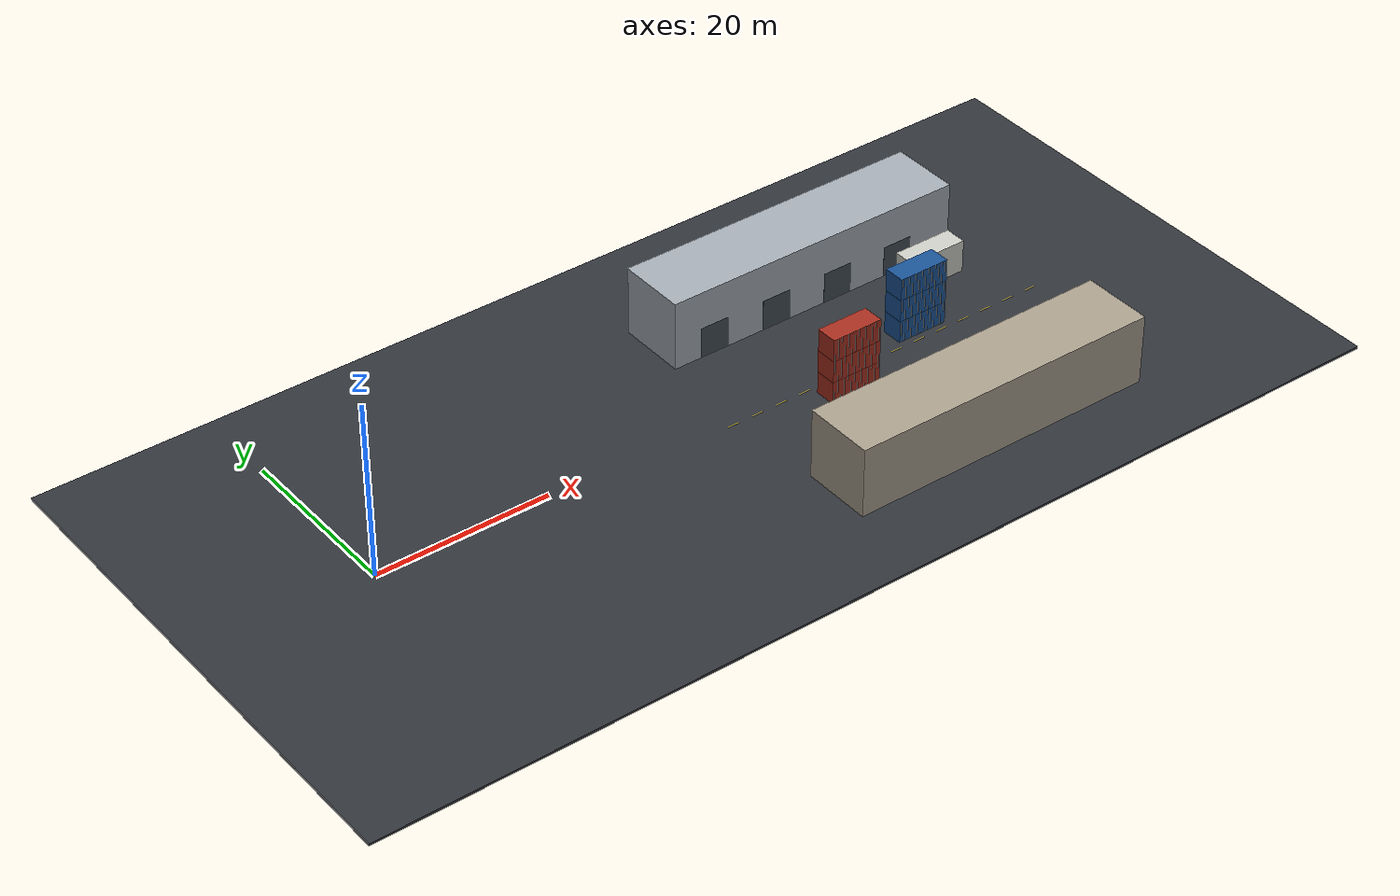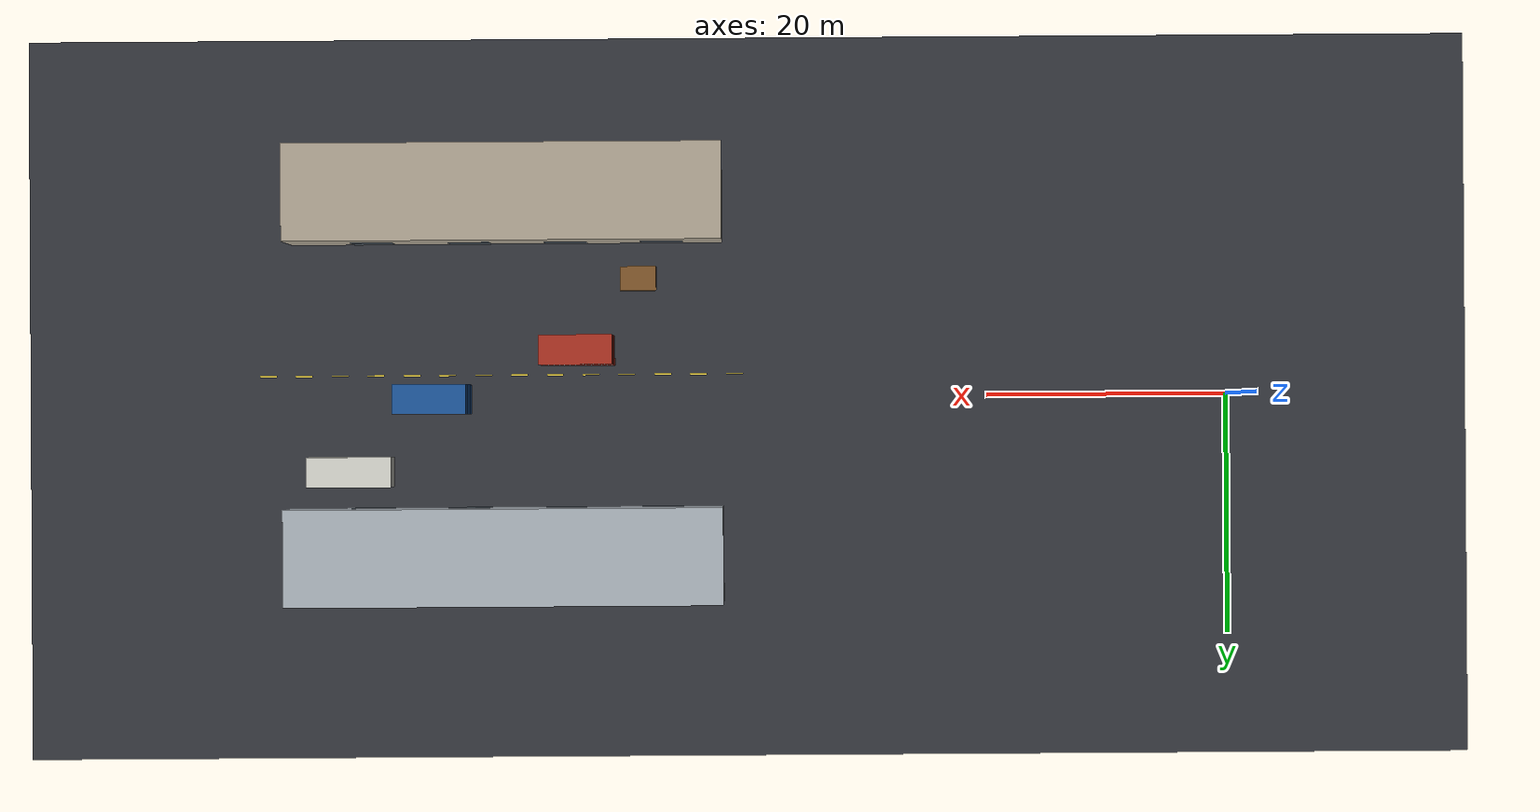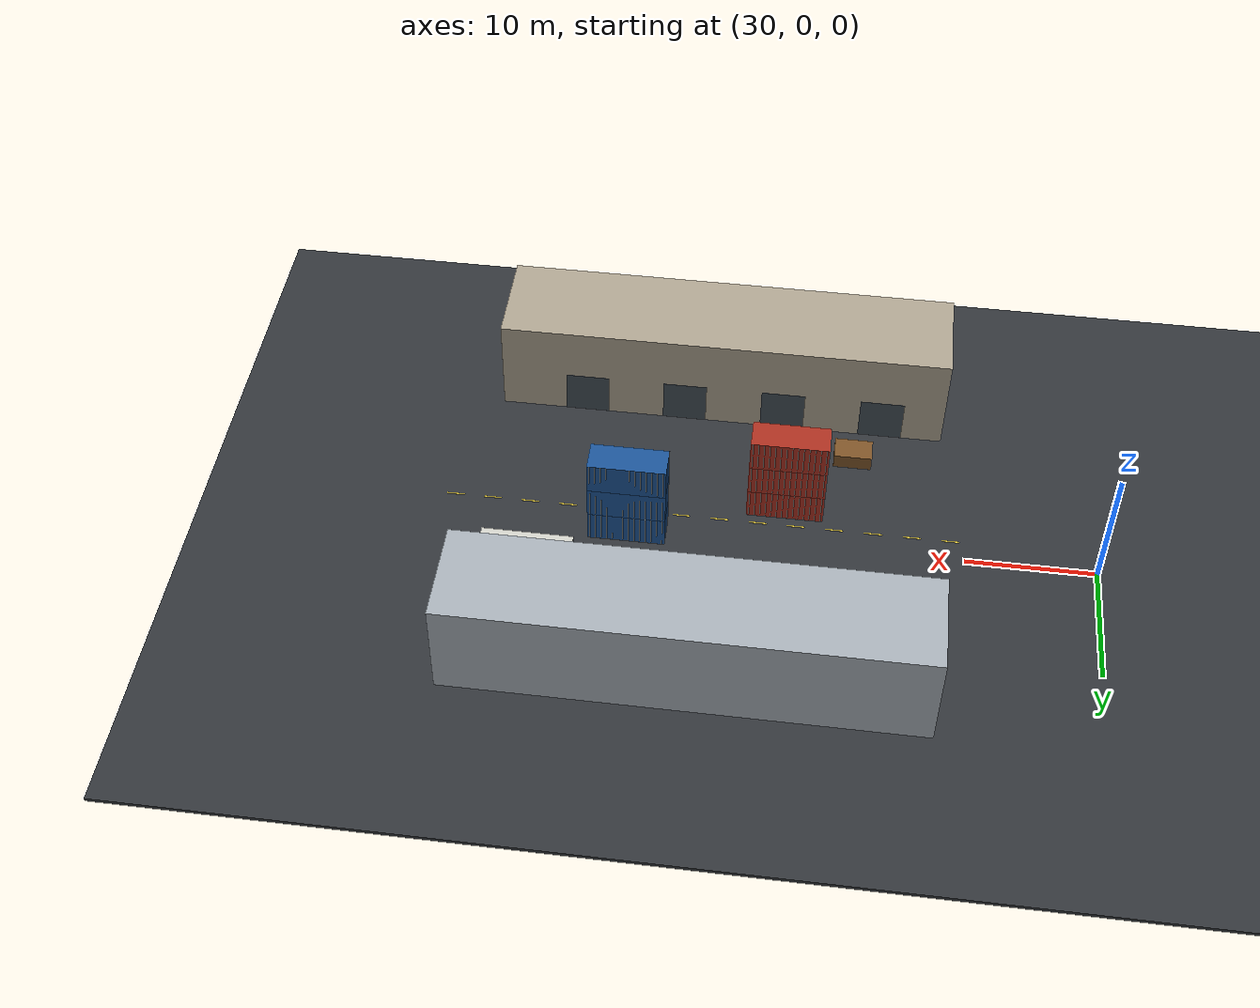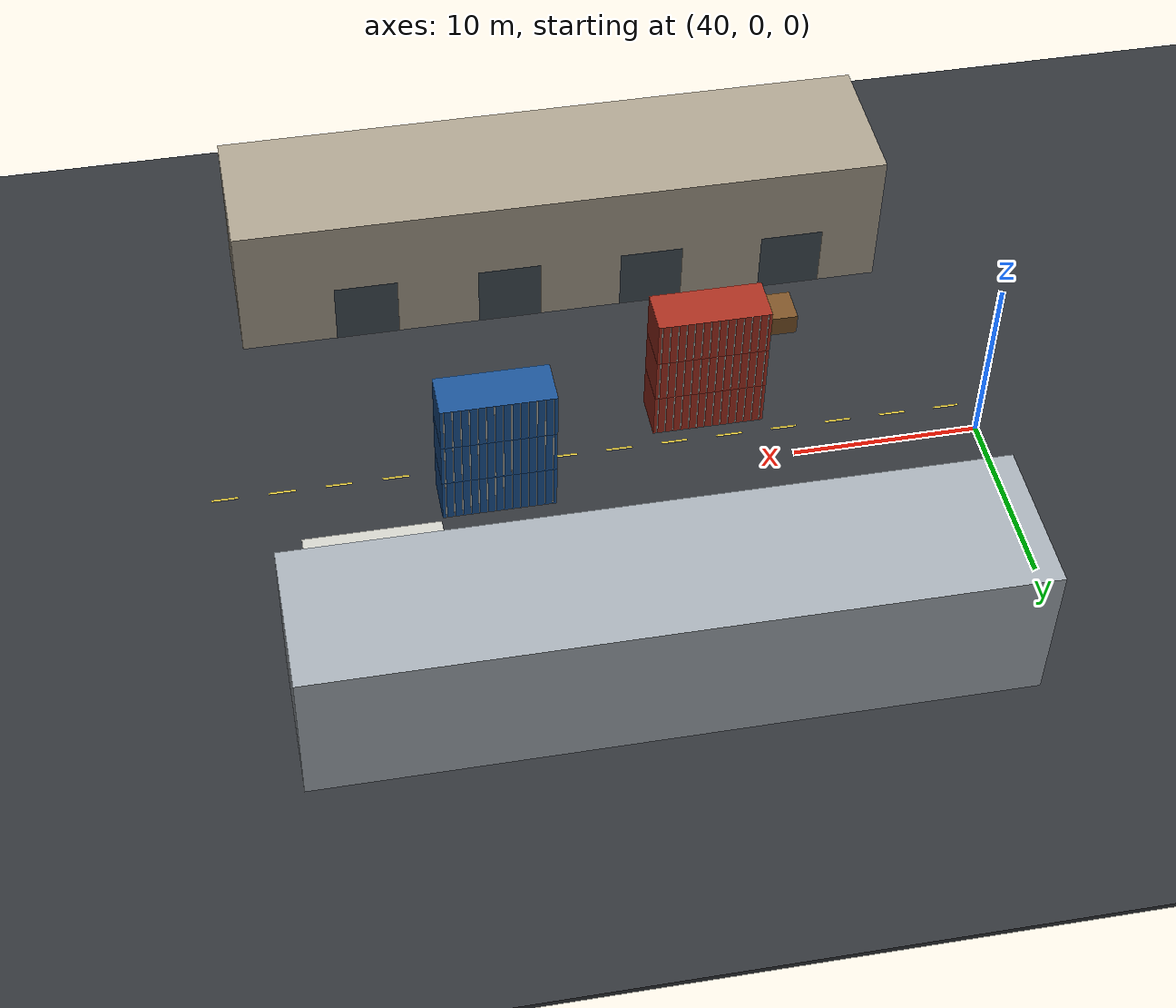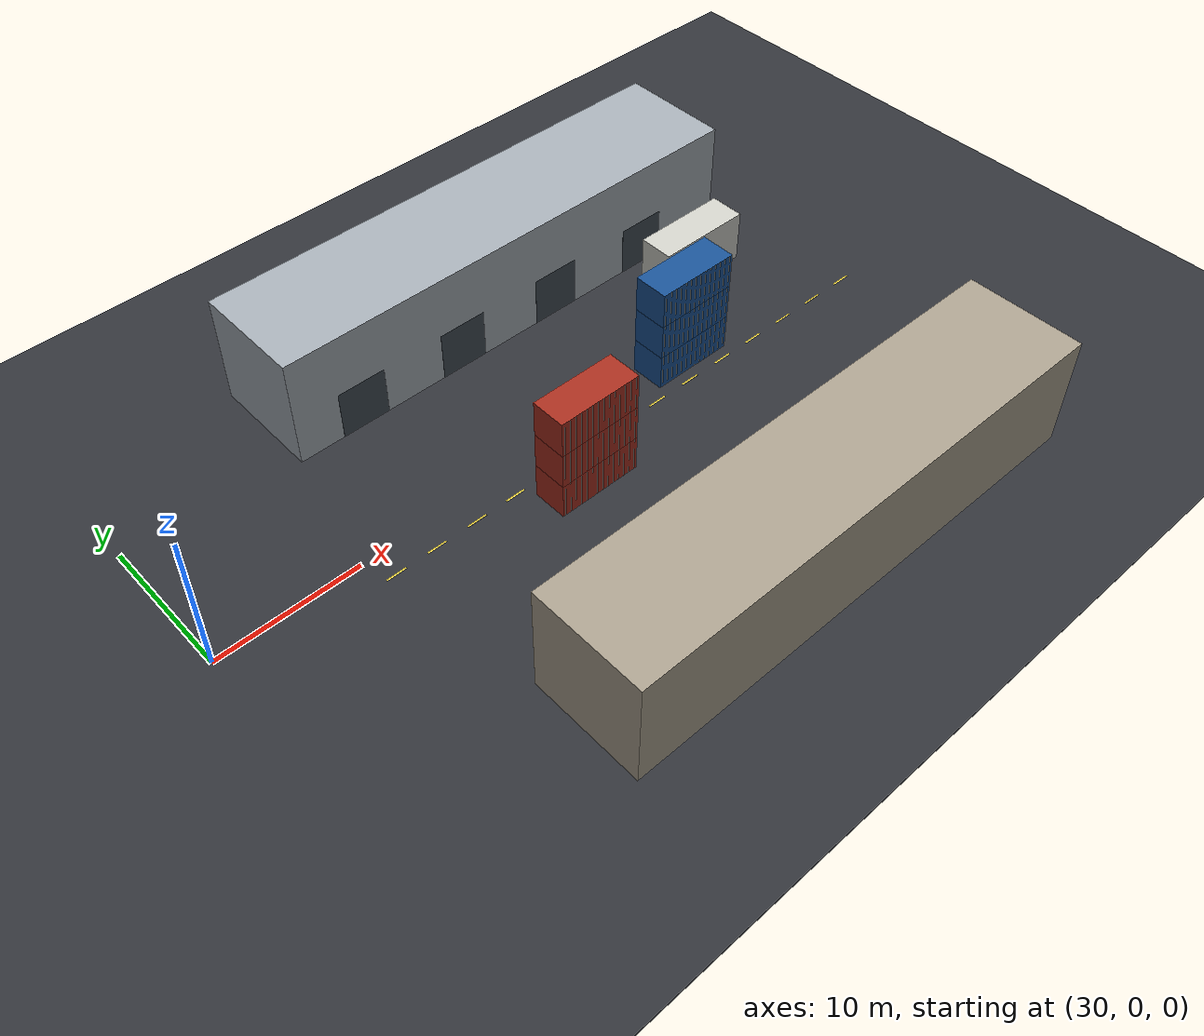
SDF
<sdf version="1.9">
 <world name="iris_mppi_yard_runup60">
  <physics name="1ms" type="ignore">
   <max_step_size>0.001</max_step_size>
   <real_time_factor>1.0</real_time_factor>
  </physics>
  <plugin filename="gz-sim-physics-system" name="gz::sim::systems::Physics"/>
  <plugin filename="gz-sim-sensors-system" name="gz::sim::systems::Sensors">
   <render_engine>ogre2</render_engine>
  </plugin>
  <plugin filename="gz-sim-user-commands-system" name="gz::sim::systems::UserCommands"/>
  <plugin filename="gz-sim-scene-broadcaster-system" name="gz::sim::systems::SceneBroadcaster"/>
  <plugin filename="gz-sim-imu-system" name="gz::sim::systems::Imu"/>
  <plugin filename="gz-sim-magnetometer-system" name="gz::sim::systems::Magnetometer"/>
  <plugin filename="gz-sim-air-pressure-system" name="gz::sim::systems::AirPressure"/>
  <plugin filename="gz-sim-navsat-system" name="gz::sim::systems::NavSat"/>
  <spherical_coordinates>
   <surface_model>EARTH_WGS84</surface_model>
   <latitude_deg>-35.363262</latitude_deg>
   <longitude_deg>149.165237</longitude_deg>
   <elevation>584</elevation>
   <heading_deg>0</heading_deg>
  </spherical_coordinates>
  <magnetic_field>2.1e-5 5.0e-6 -4.2e-5</magnetic_field>
  <scene><ambient>0.45 0.45 0.45 1</ambient><background>0.08 0.1 0.14 1</background><grid>true</grid></scene>
  <light type="directional" name="sun">
   <pose>0 0 40 0 0 0</pose>
   <diffuse>0.9 0.9 0.9 1</diffuse>
   <direction>-0.4 0.2 -1</direction>
  </light>
  <model name="asphalt">
   <static>true</static>
   <pose>40 0 -0.15 0.0 0.0 0.0</pose>
   <link name="body">
    <collision name="collision"><geometry><box><size>120 60 0.3</size></box></geometry></collision>
    <visual name="visual">
     <geometry><box><size>120 60 0.3</size></box></geometry>
     <material><ambient>.19 .20 .22 1</ambient><diffuse>.19 .20 .22 1</diffuse></material>
    </visual>
   </link>
  </model>
  <model name="north_warehouse">
   <static>true</static>
   <pose>60.1 13.1 4.0 0.0 0.0 0.0</pose>
   <link name="body">
    <collision name="collision"><geometry><box><size>36 8 8</size></box></geometry></collision>
    <visual name="visual">
     <geometry><box><size>36 8 8</size></box></geometry>
     <material><ambient>.64 .67 .70 1</ambient><diffuse>.64 .67 .70 1</diffuse></material>
    </visual>
   </link>
  </model>
  <model name="south_warehouse">
   <static>true</static>
   <pose>60.1 -16.9 4.0 0.0 0.0 0.0</pose>
   <link name="body">
    <collision name="collision"><geometry><box><size>36 8 8</size></box></geometry></collision>
    <visual name="visual">
     <geometry><box><size>36 8 8</size></box></geometry>
     <material><ambient>.66 .62 .55 1</ambient><diffuse>.66 .62 .55 1</diffuse></material>
    </visual>
   </link>
  </model>
  <model name="north_loading_door_2">
   <static>true</static>
   <pose>47.1 9.094999999999999 1.8 0.0 0.0 0.0</pose>
   <link name="body">
    <visual name="visual">
     <geometry><box><size>3.5 0.01 3.6</size></box></geometry>
     <material><ambient>.25 .29 .32 1</ambient><diffuse>.25 .29 .32 1</diffuse></material>
    </visual>
   </link>
  </model>
  <model name="south_loading_door_2">
   <static>true</static>
   <pose>47.1 -12.895 1.8 0.0 0.0 0.0</pose>
   <link name="body">
    <visual name="visual">
     <geometry><box><size>3.5 0.01 3.6</size></box></geometry>
     <material><ambient>.25 .29 .32 1</ambient><diffuse>.25 .29 .32 1</diffuse></material>
    </visual>
   </link>
  </model>
  <model name="north_loading_door_10">
   <static>true</static>
   <pose>55.1 9.094999999999999 1.8 0.0 0.0 0.0</pose>
   <link name="body">
    <visual name="visual">
     <geometry><box><size>3.5 0.01 3.6</size></box></geometry>
     <material><ambient>.25 .29 .32 1</ambient><diffuse>.25 .29 .32 1</diffuse></material>
    </visual>
   </link>
  </model>
  <model name="south_loading_door_10">
   <static>true</static>
   <pose>55.1 -12.895 1.8 0.0 0.0 0.0</pose>
   <link name="body">
    <visual name="visual">
     <geometry><box><size>3.5 0.01 3.6</size></box></geometry>
     <material><ambient>.25 .29 .32 1</ambient><diffuse>.25 .29 .32 1</diffuse></material>
    </visual>
   </link>
  </model>
  <model name="north_loading_door_18">
   <static>true</static>
   <pose>63.1 9.094999999999999 1.8 0.0 0.0 0.0</pose>
   <link name="body">
    <visual name="visual">
     <geometry><box><size>3.5 0.01 3.6</size></box></geometry>
     <material><ambient>.25 .29 .32 1</ambient><diffuse>.25 .29 .32 1</diffuse></material>
    </visual>
   </link>
  </model>
  <model name="south_loading_door_18">
   <static>true</static>
   <pose>63.1 -12.895 1.8 0.0 0.0 0.0</pose>
   <link name="body">
    <visual name="visual">
     <geometry><box><size>3.5 0.01 3.6</size></box></geometry>
     <material><ambient>.25 .29 .32 1</ambient><diffuse>.25 .29 .32 1</diffuse></material>
    </visual>
   </link>
  </model>
  <model name="north_loading_door_26">
   <static>true</static>
   <pose>71.1 9.094999999999999 1.8 0.0 0.0 0.0</pose>
   <link name="body">
    <visual name="visual">
     <geometry><box><size>3.5 0.01 3.6</size></box></geometry>
     <material><ambient>.25 .29 .32 1</ambient><diffuse>.25 .29 .32 1</diffuse></material>
    </visual>
   </link>
  </model>
  <model name="south_loading_door_26">
   <static>true</static>
   <pose>71.1 -12.895 1.8 0.0 0.0 0.0</pose>
   <link name="body">
    <visual name="visual">
     <geometry><box><size>3.5 0.01 3.6</size></box></geometry>
     <material><ambient>.25 .29 .32 1</ambient><diffuse>.25 .29 .32 1</diffuse></material>
    </visual>
   </link>
  </model>
  <model name="container_0_0">
   <static>true</static>
   <pose>54.1 -3.9 1.3 0.0 0.0 0.0</pose>
   <link name="body">
    <collision name="collision"><geometry><box><size>6 2.44 2.6</size></box></geometry></collision>
    <visual name="visual">
     <geometry><box><size>6 2.44 2.6</size></box></geometry>
     <material><ambient>.65 .18 .12 1</ambient><diffuse>.65 .18 .12 1</diffuse></material>
    </visual>
   </link>
  </model>
  <model name="rib_0_0_0_-1">
   <static>true</static>
   <pose>51.300000000000004 -5.118 1.3 0.0 0.0 0.0</pose>
   <link name="body">
    <visual name="visual">
     <geometry><box><size>0.06 0.008 2.5</size></box></geometry>
     <material><ambient>.75 .75 .72 1</ambient><diffuse>.75 .75 .72 1</diffuse></material>
    </visual>
   </link>
  </model>
  <model name="rib_0_0_0_1">
   <static>true</static>
   <pose>51.300000000000004 -2.682 1.3 0.0 0.0 0.0</pose>
   <link name="body">
    <visual name="visual">
     <geometry><box><size>0.06 0.008 2.5</size></box></geometry>
     <material><ambient>.75 .75 .72 1</ambient><diffuse>.75 .75 .72 1</diffuse></material>
    </visual>
   </link>
  </model>
  <model name="rib_0_0_1_-1">
   <static>true</static>
   <pose>51.730000000000004 -5.118 1.3 0.0 0.0 0.0</pose>
   <link name="body">
    <visual name="visual">
     <geometry><box><size>0.06 0.008 2.5</size></box></geometry>
     <material><ambient>.75 .75 .72 1</ambient><diffuse>.75 .75 .72 1</diffuse></material>
    </visual>
   </link>
  </model>
  <model name="rib_0_0_1_1">
   <static>true</static>
   <pose>51.730000000000004 -2.682 1.3 0.0 0.0 0.0</pose>
   <link name="body">
    <visual name="visual">
     <geometry><box><size>0.06 0.008 2.5</size></box></geometry>
     <material><ambient>.75 .75 .72 1</ambient><diffuse>.75 .75 .72 1</diffuse></material>
    </visual>
   </link>
  </model>
  <model name="rib_0_0_2_-1">
   <static>true</static>
   <pose>52.160000000000004 -5.118 1.3 0.0 0.0 0.0</pose>
   <link name="body">
    <visual name="visual">
     <geometry><box><size>0.06 0.008 2.5</size></box></geometry>
     <material><ambient>.75 .75 .72 1</ambient><diffuse>.75 .75 .72 1</diffuse></material>
    </visual>
   </link>
  </model>
  <model name="rib_0_0_2_1">
   <static>true</static>
   <pose>52.160000000000004 -2.682 1.3 0.0 0.0 0.0</pose>
   <link name="body">
    <visual name="visual">
     <geometry><box><size>0.06 0.008 2.5</size></box></geometry>
     <material><ambient>.75 .75 .72 1</ambient><diffuse>.75 .75 .72 1</diffuse></material>
    </visual>
   </link>
  </model>
  <model name="rib_0_0_3_-1">
   <static>true</static>
   <pose>52.59 -5.118 1.3 0.0 0.0 0.0</pose>
   <link name="body">
    <visual name="visual">
     <geometry><box><size>0.06 0.008 2.5</size></box></geometry>
     <material><ambient>.75 .75 .72 1</ambient><diffuse>.75 .75 .72 1</diffuse></material>
    </visual>
   </link>
  </model>
  <model name="rib_0_0_3_1">
   <static>true</static>
   <pose>52.59 -2.682 1.3 0.0 0.0 0.0</pose>
   <link name="body">
    <visual name="visual">
     <geometry><box><size>0.06 0.008 2.5</size></box></geometry>
     <material><ambient>.75 .75 .72 1</ambient><diffuse>.75 .75 .72 1</diffuse></material>
    </visual>
   </link>
  </model>
  <model name="rib_0_0_4_-1">
   <static>true</static>
   <pose>53.02 -5.118 1.3 0.0 0.0 0.0</pose>
   <link name="body">
    <visual name="visual">
     <geometry><box><size>0.06 0.008 2.5</size></box></geometry>
     <material><ambient>.75 .75 .72 1</ambient><diffuse>.75 .75 .72 1</diffuse></material>
    </visual>
   </link>
  </model>
  <model name="rib_0_0_4_1">
   <static>true</static>
   <pose>53.02 -2.682 1.3 0.0 0.0 0.0</pose>
   <link name="body">
    <visual name="visual">
     <geometry><box><size>0.06 0.008 2.5</size></box></geometry>
     <material><ambient>.75 .75 .72 1</ambient><diffuse>.75 .75 .72 1</diffuse></material>
    </visual>
   </link>
  </model>
  <model name="rib_0_0_5_-1">
   <static>true</static>
   <pose>53.45 -5.118 1.3 0.0 0.0 0.0</pose>
   <link name="body">
    <visual name="visual">
     <geometry><box><size>0.06 0.008 2.5</size></box></geometry>
     <material><ambient>.75 .75 .72 1</ambient><diffuse>.75 .75 .72 1</diffuse></material>
    </visual>
   </link>
  </model>
  <model name="rib_0_0_5_1">
   <static>true</static>
   <pose>53.45 -2.682 1.3 0.0 0.0 0.0</pose>
   <link name="body">
    <visual name="visual">
     <geometry><box><size>0.06 0.008 2.5</size></box></geometry>
     <material><ambient>.75 .75 .72 1</ambient><diffuse>.75 .75 .72 1</diffuse></material>
    </visual>
   </link>
  </model>
  <model name="rib_0_0_6_-1">
   <static>true</static>
   <pose>53.88 -5.118 1.3 0.0 0.0 0.0</pose>
   <link name="body">
    <visual name="visual">
     <geometry><box><size>0.06 0.008 2.5</size></box></geometry>
     <material><ambient>.75 .75 .72 1</ambient><diffuse>.75 .75 .72 1</diffuse></material>
    </visual>
   </link>
  </model>
  <model name="rib_0_0_6_1">
   <static>true</static>
   <pose>53.88 -2.682 1.3 0.0 0.0 0.0</pose>
   <link name="body">
    <visual name="visual">
     <geometry><box><size>0.06 0.008 2.5</size></box></geometry>
     <material><ambient>.75 .75 .72 1</ambient><diffuse>.75 .75 .72 1</diffuse></material>
    </visual>
   </link>
  </model>
  <model name="rib_0_0_7_-1">
   <static>true</static>
   <pose>54.31 -5.118 1.3 0.0 0.0 0.0</pose>
   <link name="body">
    <visual name="visual">
     <geometry><box><size>0.06 0.008 2.5</size></box></geometry>
     <material><ambient>.75 .75 .72 1</ambient><diffuse>.75 .75 .72 1</diffuse></material>
    </visual>
   </link>
  </model>
  <model name="rib_0_0_7_1">
   <static>true</static>
   <pose>54.31 -2.682 1.3 0.0 0.0 0.0</pose>
   <link name="body">
    <visual name="visual">
     <geometry><box><size>0.06 0.008 2.5</size></box></geometry>
     <material><ambient>.75 .75 .72 1</ambient><diffuse>.75 .75 .72 1</diffuse></material>
    </visual>
   </link>
  </model>
  <model name="rib_0_0_8_-1">
   <static>true</static>
   <pose>54.74 -5.118 1.3 0.0 0.0 0.0</pose>
   <link name="body">
    <visual name="visual">
     <geometry><box><size>0.06 0.008 2.5</size></box></geometry>
     <material><ambient>.75 .75 .72 1</ambient><diffuse>.75 .75 .72 1</diffuse></material>
    </visual>
   </link>
  </model>
  <model name="rib_0_0_8_1">
   <static>true</static>
   <pose>54.74 -2.682 1.3 0.0 0.0 0.0</pose>
   <link name="body">
    <visual name="visual">
     <geometry><box><size>0.06 0.008 2.5</size></box></geometry>
     <material><ambient>.75 .75 .72 1</ambient><diffuse>.75 .75 .72 1</diffuse></material>
    </visual>
   </link>
  </model>
  <model name="rib_0_0_9_-1">
   <static>true</static>
   <pose>55.17 -5.118 1.3 0.0 0.0 0.0</pose>
   <link name="body">
    <visual name="visual">
     <geometry><box><size>0.06 0.008 2.5</size></box></geometry>
     <material><ambient>.75 .75 .72 1</ambient><diffuse>.75 .75 .72 1</diffuse></material>
    </visual>
   </link>
  </model>
  <model name="rib_0_0_9_1">
   <static>true</static>
   <pose>55.17 -2.682 1.3 0.0 0.0 0.0</pose>
   <link name="body">
    <visual name="visual">
     <geometry><box><size>0.06 0.008 2.5</size></box></geometry>
     <material><ambient>.75 .75 .72 1</ambient><diffuse>.75 .75 .72 1</diffuse></material>
    </visual>
   </link>
  </model>
  <model name="rib_0_0_10_-1">
   <static>true</static>
   <pose>55.6 -5.118 1.3 0.0 0.0 0.0</pose>
   <link name="body">
    <visual name="visual">
     <geometry><box><size>0.06 0.008 2.5</size></box></geometry>
     <material><ambient>.75 .75 .72 1</ambient><diffuse>.75 .75 .72 1</diffuse></material>
    </visual>
   </link>
  </model>
  <model name="rib_0_0_10_1">
   <static>true</static>
   <pose>55.6 -2.682 1.3 0.0 0.0 0.0</pose>
   <link name="body">
    <visual name="visual">
     <geometry><box><size>0.06 0.008 2.5</size></box></geometry>
     <material><ambient>.75 .75 .72 1</ambient><diffuse>.75 .75 .72 1</diffuse></material>
    </visual>
   </link>
  </model>
  <model name="rib_0_0_11_-1">
   <static>true</static>
   <pose>56.03 -5.118 1.3 0.0 0.0 0.0</pose>
   <link name="body">
    <visual name="visual">
     <geometry><box><size>0.06 0.008 2.5</size></box></geometry>
     <material><ambient>.75 .75 .72 1</ambient><diffuse>.75 .75 .72 1</diffuse></material>
    </visual>
   </link>
  </model>
  <model name="rib_0_0_11_1">
   <static>true</static>
   <pose>56.03 -2.682 1.3 0.0 0.0 0.0</pose>
   <link name="body">
    <visual name="visual">
     <geometry><box><size>0.06 0.008 2.5</size></box></geometry>
     <material><ambient>.75 .75 .72 1</ambient><diffuse>.75 .75 .72 1</diffuse></material>
    </visual>
   </link>
  </model>
  <model name="rib_0_0_12_-1">
   <static>true</static>
   <pose>56.46 -5.118 1.3 0.0 0.0 0.0</pose>
   <link name="body">
    <visual name="visual">
     <geometry><box><size>0.06 0.008 2.5</size></box></geometry>
     <material><ambient>.75 .75 .72 1</ambient><diffuse>.75 .75 .72 1</diffuse></material>
    </visual>
   </link>
  </model>
  <model name="rib_0_0_12_1">
   <static>true</static>
   <pose>56.46 -2.682 1.3 0.0 0.0 0.0</pose>
   <link name="body">
    <visual name="visual">
     <geometry><box><size>0.06 0.008 2.5</size></box></geometry>
     <material><ambient>.75 .75 .72 1</ambient><diffuse>.75 .75 .72 1</diffuse></material>
    </visual>
   </link>
  </model>
  <model name="rib_0_0_13_-1">
   <static>true</static>
   <pose>56.89 -5.118 1.3 0.0 0.0 0.0</pose>
   <link name="body">
    <visual name="visual">
     <geometry><box><size>0.06 0.008 2.5</size></box></geometry>
     <material><ambient>.75 .75 .72 1</ambient><diffuse>.75 .75 .72 1</diffuse></material>
    </visual>
   </link>
  </model>
  <model name="rib_0_0_13_1">
   <static>true</static>
   <pose>56.89 -2.682 1.3 0.0 0.0 0.0</pose>
   <link name="body">
    <visual name="visual">
     <geometry><box><size>0.06 0.008 2.5</size></box></geometry>
     <material><ambient>.75 .75 .72 1</ambient><diffuse>.75 .75 .72 1</diffuse></material>
    </visual>
   </link>
  </model>
  <model name="container_0_1">
   <static>true</static>
   <pose>54.1 -3.9 3.9000000000000004 0.0 0.0 0.0</pose>
   <link name="body">
    <collision name="collision"><geometry><box><size>6 2.44 2.6</size></box></geometry></collision>
    <visual name="visual">
     <geometry><box><size>6 2.44 2.6</size></box></geometry>
     <material><ambient>.65 .18 .12 1</ambient><diffuse>.65 .18 .12 1</diffuse></material>
    </visual>
   </link>
  </model>
  <model name="rib_0_1_0_-1">
   <static>true</static>
   <pose>51.300000000000004 -5.118 3.9000000000000004 0.0 0.0 0.0</pose>
   <link name="body">
    <visual name="visual">
     <geometry><box><size>0.06 0.008 2.5</size></box></geometry>
     <material><ambient>.75 .75 .72 1</ambient><diffuse>.75 .75 .72 1</diffuse></material>
    </visual>
   </link>
  </model>
  <model name="rib_0_1_0_1">
   <static>true</static>
   <pose>51.300000000000004 -2.682 3.9000000000000004 0.0 0.0 0.0</pose>
   <link name="body">
    <visual name="visual">
     <geometry><box><size>0.06 0.008 2.5</size></box></geometry>
     <material><ambient>.75 .75 .72 1</ambient><diffuse>.75 .75 .72 1</diffuse></material>
    </visual>
   </link>
  </model>
  <model name="rib_0_1_1_-1">
   <static>true</static>
   <pose>51.730000000000004 -5.118 3.9000000000000004 0.0 0.0 0.0</pose>
   <link name="body">
    <visual name="visual">
     <geometry><box><size>0.06 0.008 2.5</size></box></geometry>
     <material><ambient>.75 .75 .72 1</ambient><diffuse>.75 .75 .72 1</diffuse></material>
    </visual>
   </link>
  </model>
  <model name="rib_0_1_1_1">
   <static>true</static>
   <pose>51.730000000000004 -2.682 3.9000000000000004 0.0 0.0 0.0</pose>
   <link name="body">
    <visual name="visual">
     <geometry><box><size>0.06 0.008 2.5</size></box></geometry>
     <material><ambient>.75 .75 .72 1</ambient><diffuse>.75 .75 .72 1</diffuse></material>
    </visual>
   </link>
  </model>
  <model name="rib_0_1_2_-1">
   <static>true</static>
   <pose>52.160000000000004 -5.118 3.9000000000000004 0.0 0.0 0.0</pose>
   <link name="body">
    <visual name="visual">
     <geometry><box><size>0.06 0.008 2.5</size></box></geometry>
     <material><ambient>.75 .75 .72 1</ambient><diffuse>.75 .75 .72 1</diffuse></material>
    </visual>
   </link>
  </model>
  <model name="rib_0_1_2_1">
   <static>true</static>
   <pose>52.160000000000004 -2.682 3.9000000000000004 0.0 0.0 0.0</pose>
   <link name="body">
    <visual name="visual">
     <geometry><box><size>0.06 0.008 2.5</size></box></geometry>
     <material><ambient>.75 .75 .72 1</ambient><diffuse>.75 .75 .72 1</diffuse></material>
    </visual>
   </link>
  </model>
  <model name="rib_0_1_3_-1">
   <static>true</static>
   <pose>52.59 -5.118 3.9000000000000004 0.0 0.0 0.0</pose>
   <link name="body">
    <visual name="visual">
     <geometry><box><size>0.06 0.008 2.5</size></box></geometry>
     <material><ambient>.75 .75 .72 1</ambient><diffuse>.75 .75 .72 1</diffuse></material>
    </visual>
   </link>
  </model>
  <model name="rib_0_1_3_1">
   <static>true</static>
   <pose>52.59 -2.682 3.9000000000000004 0.0 0.0 0.0</pose>
   <link name="body">
    <visual name="visual">
     <geometry><box><size>0.06 0.008 2.5</size></box></geometry>
     <material><ambient>.75 .75 .72 1</ambient><diffuse>.75 .75 .72 1</diffuse></material>
    </visual>
   </link>
  </model>
  <model name="rib_0_1_4_-1">
   <static>true</static>
   <pose>53.02 -5.118 3.9000000000000004 0.0 0.0 0.0</pose>
   <link name="body">
    <visual name="visual">
     <geometry><box><size>0.06 0.008 2.5</size></box></geometry>
     <material><ambient>.75 .75 .72 1</ambient><diffuse>.75 .75 .72 1</diffuse></material>
    </visual>
   </link>
  </model>
  <model name="rib_0_1_4_1">
   <static>true</static>
   <pose>53.02 -2.682 3.9000000000000004 0.0 0.0 0.0</pose>
   <link name="body">
    <visual name="visual">
     <geometry><box><size>0.06 0.008 2.5</size></box></geometry>
     <material><ambient>.75 .75 .72 1</ambient><diffuse>.75 .75 .72 1</diffuse></material>
    </visual>
   </link>
  </model>
  <model name="rib_0_1_5_-1">
   <static>true</static>
   <pose>53.45 -5.118 3.9000000000000004 0.0 0.0 0.0</pose>
   <link name="body">
    <visual name="visual">
     <geometry><box><size>0.06 0.008 2.5</size></box></geometry>
     <material><ambient>.75 .75 .72 1</ambient><diffuse>.75 .75 .72 1</diffuse></material>
    </visual>
   </link>
  </model>
  <model name="rib_0_1_5_1">
   <static>true</static>
   <pose>53.45 -2.682 3.9000000000000004 0.0 0.0 0.0</pose>
   <link name="body">
    <visual name="visual">
     <geometry><box><size>0.06 0.008 2.5</size></box></geometry>
     <material><ambient>.75 .75 .72 1</ambient><diffuse>.75 .75 .72 1</diffuse></material>
    </visual>
   </link>
  </model>
  <model name="rib_0_1_6_-1">
   <static>true</static>
   <pose>53.88 -5.118 3.9000000000000004 0.0 0.0 0.0</pose>
   <link name="body">
    <visual name="visual">
     <geometry><box><size>0.06 0.008 2.5</size></box></geometry>
     <material><ambient>.75 .75 .72 1</ambient><diffuse>.75 .75 .72 1</diffuse></material>
    </visual>
   </link>
  </model>
  <model name="rib_0_1_6_1">
   <static>true</static>
   <pose>53.88 -2.682 3.9000000000000004 0.0 0.0 0.0</pose>
   <link name="body">
    <visual name="visual">
     <geometry><box><size>0.06 0.008 2.5</size></box></geometry>
     <material><ambient>.75 .75 .72 1</ambient><diffuse>.75 .75 .72 1</diffuse></material>
    </visual>
   </link>
  </model>
  <model name="rib_0_1_7_-1">
   <static>true</static>
   <pose>54.31 -5.118 3.9000000000000004 0.0 0.0 0.0</pose>
   <link name="body">
    <visual name="visual">
     <geometry><box><size>0.06 0.008 2.5</size></box></geometry>
     <material><ambient>.75 .75 .72 1</ambient><diffuse>.75 .75 .72 1</diffuse></material>
    </visual>
   </link>
  </model>
  <model name="rib_0_1_7_1">
   <static>true</static>
   <pose>54.31 -2.682 3.9000000000000004 0.0 0.0 0.0</pose>
   <link name="body">
    <visual name="visual">
     <geometry><box><size>0.06 0.008 2.5</size></box></geometry>
     <material><ambient>.75 .75 .72 1</ambient><diffuse>.75 .75 .72 1</diffuse></material>
    </visual>
   </link>
  </model>
  <model name="rib_0_1_8_-1">
   <static>true</static>
   <pose>54.74 -5.118 3.9000000000000004 0.0 0.0 0.0</pose>
   <link name="body">
    <visual name="visual">
     <geometry><box><size>0.06 0.008 2.5</size></box></geometry>
     <material><ambient>.75 .75 .72 1</ambient><diffuse>.75 .75 .72 1</diffuse></material>
    </visual>
   </link>
  </model>
  <model name="rib_0_1_8_1">
   <static>true</static>
   <pose>54.74 -2.682 3.9000000000000004 0.0 0.0 0.0</pose>
   <link name="body">
    <visual name="visual">
     <geometry><box><size>0.06 0.008 2.5</size></box></geometry>
     <material><ambient>.75 .75 .72 1</ambient><diffuse>.75 .75 .72 1</diffuse></material>
    </visual>
   </link>
  </model>
  <model name="rib_0_1_9_-1">
   <static>true</static>
   <pose>55.17 -5.118 3.9000000000000004 0.0 0.0 0.0</pose>
   <link name="body">
    <visual name="visual">
     <geometry><box><size>0.06 0.008 2.5</size></box></geometry>
     <material><ambient>.75 .75 .72 1</ambient><diffuse>.75 .75 .72 1</diffuse></material>
    </visual>
   </link>
  </model>
  <model name="rib_0_1_9_1">
   <static>true</static>
   <pose>55.17 -2.682 3.9000000000000004 0.0 0.0 0.0</pose>
   <link name="body">
    <visual name="visual">
     <geometry><box><size>0.06 0.008 2.5</size></box></geometry>
     <material><ambient>.75 .75 .72 1</ambient><diffuse>.75 .75 .72 1</diffuse></material>
    </visual>
   </link>
  </model>
  <model name="rib_0_1_10_-1">
   <static>true</static>
   <pose>55.6 -5.118 3.9000000000000004 0.0 0.0 0.0</pose>
   <link name="body">
    <visual name="visual">
     <geometry><box><size>0.06 0.008 2.5</size></box></geometry>
     <material><ambient>.75 .75 .72 1</ambient><diffuse>.75 .75 .72 1</diffuse></material>
    </visual>
   </link>
  </model>
  <model name="rib_0_1_10_1">
   <static>true</static>
   <pose>55.6 -2.682 3.9000000000000004 0.0 0.0 0.0</pose>
   <link name="body">
    <visual name="visual">
     <geometry><box><size>0.06 0.008 2.5</size></box></geometry>
     <material><ambient>.75 .75 .72 1</ambient><diffuse>.75 .75 .72 1</diffuse></material>
    </visual>
   </link>
  </model>
  <model name="rib_0_1_11_-1">
   <static>true</static>
   <pose>56.03 -5.118 3.9000000000000004 0.0 0.0 0.0</pose>
   <link name="body">
    <visual name="visual">
     <geometry><box><size>0.06 0.008 2.5</size></box></geometry>
     <material><ambient>.75 .75 .72 1</ambient><diffuse>.75 .75 .72 1</diffuse></material>
    </visual>
   </link>
  </model>
  <model name="rib_0_1_11_1">
   <static>true</static>
   <pose>56.03 -2.682 3.9000000000000004 0.0 0.0 0.0</pose>
   <link name="body">
    <visual name="visual">
     <geometry><box><size>0.06 0.008 2.5</size></box></geometry>
     <material><ambient>.75 .75 .72 1</ambient><diffuse>.75 .75 .72 1</diffuse></material>
    </visual>
   </link>
  </model>
  <model name="rib_0_1_12_-1">
   <static>true</static>
   <pose>56.46 -5.118 3.9000000000000004 0.0 0.0 0.0</pose>
   <link name="body">
    <visual name="visual">
     <geometry><box><size>0.06 0.008 2.5</size></box></geometry>
     <material><ambient>.75 .75 .72 1</ambient><diffuse>.75 .75 .72 1</diffuse></material>
    </visual>
   </link>
  </model>
  <model name="rib_0_1_12_1">
   <static>true</static>
   <pose>56.46 -2.682 3.9000000000000004 0.0 0.0 0.0</pose>
   <link name="body">
    <visual name="visual">
     <geometry><box><size>0.06 0.008 2.5</size></box></geometry>
     <material><ambient>.75 .75 .72 1</ambient><diffuse>.75 .75 .72 1</diffuse></material>
    </visual>
   </link>
  </model>
  <model name="rib_0_1_13_-1">
   <static>true</static>
   <pose>56.89 -5.118 3.9000000000000004 0.0 0.0 0.0</pose>
   <link name="body">
    <visual name="visual">
     <geometry><box><size>0.06 0.008 2.5</size></box></geometry>
     <material><ambient>.75 .75 .72 1</ambient><diffuse>.75 .75 .72 1</diffuse></material>
    </visual>
   </link>
  </model>
  <model name="rib_0_1_13_1">
   <static>true</static>
   <pose>56.89 -2.682 3.9000000000000004 0.0 0.0 0.0</pose>
   <link name="body">
    <visual name="visual">
     <geometry><box><size>0.06 0.008 2.5</size></box></geometry>
     <material><ambient>.75 .75 .72 1</ambient><diffuse>.75 .75 .72 1</diffuse></material>
    </visual>
   </link>
  </model>
  <model name="container_0_2">
   <static>true</static>
   <pose>54.1 -3.9 6.5 0.0 0.0 0.0</pose>
   <link name="body">
    <collision name="collision"><geometry><box><size>6 2.44 2.6</size></box></geometry></collision>
    <visual name="visual">
     <geometry><box><size>6 2.44 2.6</size></box></geometry>
     <material><ambient>.65 .18 .12 1</ambient><diffuse>.65 .18 .12 1</diffuse></material>
    </visual>
   </link>
  </model>
  <model name="rib_0_2_0_-1">
   <static>true</static>
   <pose>51.300000000000004 -5.118 6.5 0.0 0.0 0.0</pose>
   <link name="body">
    <visual name="visual">
     <geometry><box><size>0.06 0.008 2.5</size></box></geometry>
     <material><ambient>.75 .75 .72 1</ambient><diffuse>.75 .75 .72 1</diffuse></material>
    </visual>
   </link>
  </model>
  <model name="rib_0_2_0_1">
   <static>true</static>
   <pose>51.300000000000004 -2.682 6.5 0.0 0.0 0.0</pose>
   <link name="body">
    <visual name="visual">
     <geometry><box><size>0.06 0.008 2.5</size></box></geometry>
     <material><ambient>.75 .75 .72 1</ambient><diffuse>.75 .75 .72 1</diffuse></material>
    </visual>
   </link>
  </model>
  <model name="rib_0_2_1_-1">
   <static>true</static>
   <pose>51.730000000000004 -5.118 6.5 0.0 0.0 0.0</pose>
   <link name="body">
    <visual name="visual">
     <geometry><box><size>0.06 0.008 2.5</size></box></geometry>
     <material><ambient>.75 .75 .72 1</ambient><diffuse>.75 .75 .72 1</diffuse></material>
    </visual>
   </link>
  </model>
  <model name="rib_0_2_1_1">
   <static>true</static>
   <pose>51.730000000000004 -2.682 6.5 0.0 0.0 0.0</pose>
   <link name="body">
    <visual name="visual">
     <geometry><box><size>0.06 0.008 2.5</size></box></geometry>
     <material><ambient>.75 .75 .72 1</ambient><diffuse>.75 .75 .72 1</diffuse></material>
    </visual>
   </link>
  </model>
  <model name="rib_0_2_2_-1">
   <static>true</static>
   <pose>52.160000000000004 -5.118 6.5 0.0 0.0 0.0</pose>
   <link name="body">
    <visual name="visual">
     <geometry><box><size>0.06 0.008 2.5</size></box></geometry>
     <material><ambient>.75 .75 .72 1</ambient><diffuse>.75 .75 .72 1</diffuse></material>
    </visual>
   </link>
  </model>
  <model name="rib_0_2_2_1">
   <static>true</static>
   <pose>52.160000000000004 -2.682 6.5 0.0 0.0 0.0</pose>
   <link name="body">
    <visual name="visual">
     <geometry><box><size>0.06 0.008 2.5</size></box></geometry>
     <material><ambient>.75 .75 .72 1</ambient><diffuse>.75 .75 .72 1</diffuse></material>
    </visual>
   </link>
  </model>
  <model name="rib_0_2_3_-1">
   <static>true</static>
   <pose>52.59 -5.118 6.5 0.0 0.0 0.0</pose>
   <link name="body">
    <visual name="visual">
     <geometry><box><size>0.06 0.008 2.5</size></box></geometry>
     <material><ambient>.75 .75 .72 1</ambient><diffuse>.75 .75 .72 1</diffuse></material>
    </visual>
   </link>
  </model>
  <model name="rib_0_2_3_1">
   <static>true</static>
   <pose>52.59 -2.682 6.5 0.0 0.0 0.0</pose>
   <link name="body">
    <visual name="visual">
     <geometry><box><size>0.06 0.008 2.5</size></box></geometry>
     <material><ambient>.75 .75 .72 1</ambient><diffuse>.75 .75 .72 1</diffuse></material>
    </visual>
   </link>
  </model>
  <model name="rib_0_2_4_-1">
   <static>true</static>
   <pose>53.02 -5.118 6.5 0.0 0.0 0.0</pose>
   <link name="body">
    <visual name="visual">
     <geometry><box><size>0.06 0.008 2.5</size></box></geometry>
     <material><ambient>.75 .75 .72 1</ambient><diffuse>.75 .75 .72 1</diffuse></material>
    </visual>
   </link>
  </model>
  <model name="rib_0_2_4_1">
   <static>true</static>
   <pose>53.02 -2.682 6.5 0.0 0.0 0.0</pose>
   <link name="body">
    <visual name="visual">
     <geometry><box><size>0.06 0.008 2.5</size></box></geometry>
     <material><ambient>.75 .75 .72 1</ambient><diffuse>.75 .75 .72 1</diffuse></material>
    </visual>
   </link>
  </model>
  <model name="rib_0_2_5_-1">
   <static>true</static>
   <pose>53.45 -5.118 6.5 0.0 0.0 0.0</pose>
   <link name="body">
    <visual name="visual">
     <geometry><box><size>0.06 0.008 2.5</size></box></geometry>
     <material><ambient>.75 .75 .72 1</ambient><diffuse>.75 .75 .72 1</diffuse></material>
    </visual>
   </link>
  </model>
  <model name="rib_0_2_5_1">
   <static>true</static>
   <pose>53.45 -2.682 6.5 0.0 0.0 0.0</pose>
   <link name="body">
    <visual name="visual">
     <geometry><box><size>0.06 0.008 2.5</size></box></geometry>
     <material><ambient>.75 .75 .72 1</ambient><diffuse>.75 .75 .72 1</diffuse></material>
    </visual>
   </link>
  </model>
  <model name="rib_0_2_6_-1">
   <static>true</static>
   <pose>53.88 -5.118 6.5 0.0 0.0 0.0</pose>
   <link name="body">
    <visual name="visual">
     <geometry><box><size>0.06 0.008 2.5</size></box></geometry>
     <material><ambient>.75 .75 .72 1</ambient><diffuse>.75 .75 .72 1</diffuse></material>
    </visual>
   </link>
  </model>
  <model name="rib_0_2_6_1">
   <static>true</static>
   <pose>53.88 -2.682 6.5 0.0 0.0 0.0</pose>
   <link name="body">
    <visual name="visual">
     <geometry><box><size>0.06 0.008 2.5</size></box></geometry>
     <material><ambient>.75 .75 .72 1</ambient><diffuse>.75 .75 .72 1</diffuse></material>
    </visual>
   </link>
  </model>
  <model name="rib_0_2_7_-1">
   <static>true</static>
   <pose>54.31 -5.118 6.5 0.0 0.0 0.0</pose>
   <link name="body">
    <visual name="visual">
     <geometry><box><size>0.06 0.008 2.5</size></box></geometry>
     <material><ambient>.75 .75 .72 1</ambient><diffuse>.75 .75 .72 1</diffuse></material>
    </visual>
   </link>
  </model>
  <model name="rib_0_2_7_1">
   <static>true</static>
   <pose>54.31 -2.682 6.5 0.0 0.0 0.0</pose>
   <link name="body">
    <visual name="visual">
     <geometry><box><size>0.06 0.008 2.5</size></box></geometry>
     <material><ambient>.75 .75 .72 1</ambient><diffuse>.75 .75 .72 1</diffuse></material>
    </visual>
   </link>
  </model>
  <model name="rib_0_2_8_-1">
   <static>true</static>
   <pose>54.74 -5.118 6.5 0.0 0.0 0.0</pose>
   <link name="body">
    <visual name="visual">
     <geometry><box><size>0.06 0.008 2.5</size></box></geometry>
     <material><ambient>.75 .75 .72 1</ambient><diffuse>.75 .75 .72 1</diffuse></material>
    </visual>
   </link>
  </model>
  <model name="rib_0_2_8_1">
   <static>true</static>
   <pose>54.74 -2.682 6.5 0.0 0.0 0.0</pose>
   <link name="body">
    <visual name="visual">
     <geometry><box><size>0.06 0.008 2.5</size></box></geometry>
     <material><ambient>.75 .75 .72 1</ambient><diffuse>.75 .75 .72 1</diffuse></material>
    </visual>
   </link>
  </model>
  <model name="rib_0_2_9_-1">
   <static>true</static>
   <pose>55.17 -5.118 6.5 0.0 0.0 0.0</pose>
   <link name="body">
    <visual name="visual">
     <geometry><box><size>0.06 0.008 2.5</size></box></geometry>
     <material><ambient>.75 .75 .72 1</ambient><diffuse>.75 .75 .72 1</diffuse></material>
    </visual>
   </link>
  </model>
  <model name="rib_0_2_9_1">
   <static>true</static>
   <pose>55.17 -2.682 6.5 0.0 0.0 0.0</pose>
   <link name="body">
    <visual name="visual">
     <geometry><box><size>0.06 0.008 2.5</size></box></geometry>
     <material><ambient>.75 .75 .72 1</ambient><diffuse>.75 .75 .72 1</diffuse></material>
    </visual>
   </link>
  </model>
  <model name="rib_0_2_10_-1">
   <static>true</static>
   <pose>55.6 -5.118 6.5 0.0 0.0 0.0</pose>
   <link name="body">
    <visual name="visual">
     <geometry><box><size>0.06 0.008 2.5</size></box></geometry>
     <material><ambient>.75 .75 .72 1</ambient><diffuse>.75 .75 .72 1</diffuse></material>
    </visual>
   </link>
  </model>
  <model name="rib_0_2_10_1">
   <static>true</static>
   <pose>55.6 -2.682 6.5 0.0 0.0 0.0</pose>
   <link name="body">
    <visual name="visual">
     <geometry><box><size>0.06 0.008 2.5</size></box></geometry>
     <material><ambient>.75 .75 .72 1</ambient><diffuse>.75 .75 .72 1</diffuse></material>
    </visual>
   </link>
  </model>
  <model name="rib_0_2_11_-1">
   <static>true</static>
   <pose>56.03 -5.118 6.5 0.0 0.0 0.0</pose>
   <link name="body">
    <visual name="visual">
     <geometry><box><size>0.06 0.008 2.5</size></box></geometry>
     <material><ambient>.75 .75 .72 1</ambient><diffuse>.75 .75 .72 1</diffuse></material>
    </visual>
   </link>
  </model>
  <model name="rib_0_2_11_1">
   <static>true</static>
   <pose>56.03 -2.682 6.5 0.0 0.0 0.0</pose>
   <link name="body">
    <visual name="visual">
     <geometry><box><size>0.06 0.008 2.5</size></box></geometry>
     <material><ambient>.75 .75 .72 1</ambient><diffuse>.75 .75 .72 1</diffuse></material>
    </visual>
   </link>
  </model>
  <model name="rib_0_2_12_-1">
   <static>true</static>
   <pose>56.46 -5.118 6.5 0.0 0.0 0.0</pose>
   <link name="body">
    <visual name="visual">
     <geometry><box><size>0.06 0.008 2.5</size></box></geometry>
     <material><ambient>.75 .75 .72 1</ambient><diffuse>.75 .75 .72 1</diffuse></material>
    </visual>
   </link>
  </model>
  <model name="rib_0_2_12_1">
   <static>true</static>
   <pose>56.46 -2.682 6.5 0.0 0.0 0.0</pose>
   <link name="body">
    <visual name="visual">
     <geometry><box><size>0.06 0.008 2.5</size></box></geometry>
     <material><ambient>.75 .75 .72 1</ambient><diffuse>.75 .75 .72 1</diffuse></material>
    </visual>
   </link>
  </model>
  <model name="rib_0_2_13_-1">
   <static>true</static>
   <pose>56.89 -5.118 6.5 0.0 0.0 0.0</pose>
   <link name="body">
    <visual name="visual">
     <geometry><box><size>0.06 0.008 2.5</size></box></geometry>
     <material><ambient>.75 .75 .72 1</ambient><diffuse>.75 .75 .72 1</diffuse></material>
    </visual>
   </link>
  </model>
  <model name="rib_0_2_13_1">
   <static>true</static>
   <pose>56.89 -2.682 6.5 0.0 0.0 0.0</pose>
   <link name="body">
    <visual name="visual">
     <geometry><box><size>0.06 0.008 2.5</size></box></geometry>
     <material><ambient>.75 .75 .72 1</ambient><diffuse>.75 .75 .72 1</diffuse></material>
    </visual>
   </link>
  </model>
  <model name="container_1_0">
   <static>true</static>
   <pose>66.1 0.10000000000000009 1.3 0.0 0.0 0.0</pose>
   <link name="body">
    <collision name="collision"><geometry><box><size>6 2.44 2.6</size></box></geometry></collision>
    <visual name="visual">
     <geometry><box><size>6 2.44 2.6</size></box></geometry>
     <material><ambient>.10 .32 .58 1</ambient><diffuse>.10 .32 .58 1</diffuse></material>
    </visual>
   </link>
  </model>
  <model name="rib_1_0_0_-1">
   <static>true</static>
   <pose>63.3 -1.1179999999999999 1.3 0.0 0.0 0.0</pose>
   <link name="body">
    <visual name="visual">
     <geometry><box><size>0.06 0.008 2.5</size></box></geometry>
     <material><ambient>.75 .75 .72 1</ambient><diffuse>.75 .75 .72 1</diffuse></material>
    </visual>
   </link>
  </model>
  <model name="rib_1_0_0_1">
   <static>true</static>
   <pose>63.3 1.318 1.3 0.0 0.0 0.0</pose>
   <link name="body">
    <visual name="visual">
     <geometry><box><size>0.06 0.008 2.5</size></box></geometry>
     <material><ambient>.75 .75 .72 1</ambient><diffuse>.75 .75 .72 1</diffuse></material>
    </visual>
   </link>
  </model>
  <model name="rib_1_0_1_-1">
   <static>true</static>
   <pose>63.730000000000004 -1.1179999999999999 1.3 0.0 0.0 0.0</pose>
   <link name="body">
    <visual name="visual">
     <geometry><box><size>0.06 0.008 2.5</size></box></geometry>
     <material><ambient>.75 .75 .72 1</ambient><diffuse>.75 .75 .72 1</diffuse></material>
    </visual>
   </link>
  </model>
  <model name="rib_1_0_1_1">
   <static>true</static>
   <pose>63.730000000000004 1.318 1.3 0.0 0.0 0.0</pose>
   <link name="body">
    <visual name="visual">
     <geometry><box><size>0.06 0.008 2.5</size></box></geometry>
     <material><ambient>.75 .75 .72 1</ambient><diffuse>.75 .75 .72 1</diffuse></material>
    </visual>
   </link>
  </model>
  <model name="rib_1_0_2_-1">
   <static>true</static>
   <pose>64.16 -1.1179999999999999 1.3 0.0 0.0 0.0</pose>
   <link name="body">
    <visual name="visual">
     <geometry><box><size>0.06 0.008 2.5</size></box></geometry>
     <material><ambient>.75 .75 .72 1</ambient><diffuse>.75 .75 .72 1</diffuse></material>
    </visual>
   </link>
  </model>
  <model name="rib_1_0_2_1">
   <static>true</static>
   <pose>64.16 1.318 1.3 0.0 0.0 0.0</pose>
   <link name="body">
    <visual name="visual">
     <geometry><box><size>0.06 0.008 2.5</size></box></geometry>
     <material><ambient>.75 .75 .72 1</ambient><diffuse>.75 .75 .72 1</diffuse></material>
    </visual>
   </link>
  </model>
  <model name="rib_1_0_3_-1">
   <static>true</static>
   <pose>64.59 -1.1179999999999999 1.3 0.0 0.0 0.0</pose>
   <link name="body">
    <visual name="visual">
     <geometry><box><size>0.06 0.008 2.5</size></box></geometry>
     <material><ambient>.75 .75 .72 1</ambient><diffuse>.75 .75 .72 1</diffuse></material>
    </visual>
   </link>
  </model>
  <model name="rib_1_0_3_1">
   <static>true</static>
   <pose>64.59 1.318 1.3 0.0 0.0 0.0</pose>
   <link name="body">
    <visual name="visual">
     <geometry><box><size>0.06 0.008 2.5</size></box></geometry>
     <material><ambient>.75 .75 .72 1</ambient><diffuse>.75 .75 .72 1</diffuse></material>
    </visual>
   </link>
  </model>
  <model name="rib_1_0_4_-1">
   <static>true</static>
   <pose>65.02 -1.1179999999999999 1.3 0.0 0.0 0.0</pose>
   <link name="body">
    <visual name="visual">
     <geometry><box><size>0.06 0.008 2.5</size></box></geometry>
     <material><ambient>.75 .75 .72 1</ambient><diffuse>.75 .75 .72 1</diffuse></material>
    </visual>
   </link>
  </model>
  <model name="rib_1_0_4_1">
   <static>true</static>
   <pose>65.02 1.318 1.3 0.0 0.0 0.0</pose>
   <link name="body">
    <visual name="visual">
     <geometry><box><size>0.06 0.008 2.5</size></box></geometry>
     <material><ambient>.75 .75 .72 1</ambient><diffuse>.75 .75 .72 1</diffuse></material>
    </visual>
   </link>
  </model>
  <model name="rib_1_0_5_-1">
   <static>true</static>
   <pose>65.45 -1.1179999999999999 1.3 0.0 0.0 0.0</pose>
   <link name="body">
    <visual name="visual">
     <geometry><box><size>0.06 0.008 2.5</size></box></geometry>
     <material><ambient>.75 .75 .72 1</ambient><diffuse>.75 .75 .72 1</diffuse></material>
    </visual>
   </link>
  </model>
  <model name="rib_1_0_5_1">
   <static>true</static>
   <pose>65.45 1.318 1.3 0.0 0.0 0.0</pose>
   <link name="body">
    <visual name="visual">
     <geometry><box><size>0.06 0.008 2.5</size></box></geometry>
     <material><ambient>.75 .75 .72 1</ambient><diffuse>.75 .75 .72 1</diffuse></material>
    </visual>
   </link>
  </model>
  <model name="rib_1_0_6_-1">
   <static>true</static>
   <pose>65.88 -1.1179999999999999 1.3 0.0 0.0 0.0</pose>
   <link name="body">
    <visual name="visual">
     <geometry><box><size>0.06 0.008 2.5</size></box></geometry>
     <material><ambient>.75 .75 .72 1</ambient><diffuse>.75 .75 .72 1</diffuse></material>
    </visual>
   </link>
  </model>
  <model name="rib_1_0_6_1">
   <static>true</static>
   <pose>65.88 1.318 1.3 0.0 0.0 0.0</pose>
   <link name="body">
    <visual name="visual">
     <geometry><box><size>0.06 0.008 2.5</size></box></geometry>
     <material><ambient>.75 .75 .72 1</ambient><diffuse>.75 .75 .72 1</diffuse></material>
    </visual>
   </link>
  </model>
  <model name="rib_1_0_7_-1">
   <static>true</static>
   <pose>66.31 -1.1179999999999999 1.3 0.0 0.0 0.0</pose>
   <link name="body">
    <visual name="visual">
     <geometry><box><size>0.06 0.008 2.5</size></box></geometry>
     <material><ambient>.75 .75 .72 1</ambient><diffuse>.75 .75 .72 1</diffuse></material>
    </visual>
   </link>
  </model>
  <model name="rib_1_0_7_1">
   <static>true</static>
   <pose>66.31 1.318 1.3 0.0 0.0 0.0</pose>
   <link name="body">
    <visual name="visual">
     <geometry><box><size>0.06 0.008 2.5</size></box></geometry>
     <material><ambient>.75 .75 .72 1</ambient><diffuse>.75 .75 .72 1</diffuse></material>
    </visual>
   </link>
  </model>
  <model name="rib_1_0_8_-1">
   <static>true</static>
   <pose>66.74000000000001 -1.1179999999999999 1.3 0.0 0.0 0.0</pose>
   <link name="body">
    <visual name="visual">
     <geometry><box><size>0.06 0.008 2.5</size></box></geometry>
     <material><ambient>.75 .75 .72 1</ambient><diffuse>.75 .75 .72 1</diffuse></material>
    </visual>
   </link>
  </model>
  <model name="rib_1_0_8_1">
   <static>true</static>
   <pose>66.74000000000001 1.318 1.3 0.0 0.0 0.0</pose>
   <link name="body">
    <visual name="visual">
     <geometry><box><size>0.06 0.008 2.5</size></box></geometry>
     <material><ambient>.75 .75 .72 1</ambient><diffuse>.75 .75 .72 1</diffuse></material>
    </visual>
   </link>
  </model>
  <model name="rib_1_0_9_-1">
   <static>true</static>
   <pose>67.17 -1.1179999999999999 1.3 0.0 0.0 0.0</pose>
   <link name="body">
    <visual name="visual">
     <geometry><box><size>0.06 0.008 2.5</size></box></geometry>
     <material><ambient>.75 .75 .72 1</ambient><diffuse>.75 .75 .72 1</diffuse></material>
    </visual>
   </link>
  </model>
  <model name="rib_1_0_9_1">
   <static>true</static>
   <pose>67.17 1.318 1.3 0.0 0.0 0.0</pose>
   <link name="body">
    <visual name="visual">
     <geometry><box><size>0.06 0.008 2.5</size></box></geometry>
     <material><ambient>.75 .75 .72 1</ambient><diffuse>.75 .75 .72 1</diffuse></material>
    </visual>
   </link>
  </model>
  <model name="rib_1_0_10_-1">
   <static>true</static>
   <pose>67.6 -1.1179999999999999 1.3 0.0 0.0 0.0</pose>
   <link name="body">
    <visual name="visual">
     <geometry><box><size>0.06 0.008 2.5</size></box></geometry>
     <material><ambient>.75 .75 .72 1</ambient><diffuse>.75 .75 .72 1</diffuse></material>
    </visual>
   </link>
  </model>
  <model name="rib_1_0_10_1">
   <static>true</static>
   <pose>67.6 1.318 1.3 0.0 0.0 0.0</pose>
   <link name="body">
    <visual name="visual">
     <geometry><box><size>0.06 0.008 2.5</size></box></geometry>
     <material><ambient>.75 .75 .72 1</ambient><diffuse>.75 .75 .72 1</diffuse></material>
    </visual>
   </link>
  </model>
  <model name="rib_1_0_11_-1">
   <static>true</static>
   <pose>68.03 -1.1179999999999999 1.3 0.0 0.0 0.0</pose>
   <link name="body">
    <visual name="visual">
     <geometry><box><size>0.06 0.008 2.5</size></box></geometry>
     <material><ambient>.75 .75 .72 1</ambient><diffuse>.75 .75 .72 1</diffuse></material>
    </visual>
   </link>
  </model>
  <model name="rib_1_0_11_1">
   <static>true</static>
   <pose>68.03 1.318 1.3 0.0 0.0 0.0</pose>
   <link name="body">
    <visual name="visual">
     <geometry><box><size>0.06 0.008 2.5</size></box></geometry>
     <material><ambient>.75 .75 .72 1</ambient><diffuse>.75 .75 .72 1</diffuse></material>
    </visual>
   </link>
  </model>
  <model name="rib_1_0_12_-1">
   <static>true</static>
   <pose>68.46000000000001 -1.1179999999999999 1.3 0.0 0.0 0.0</pose>
   <link name="body">
    <visual name="visual">
     <geometry><box><size>0.06 0.008 2.5</size></box></geometry>
     <material><ambient>.75 .75 .72 1</ambient><diffuse>.75 .75 .72 1</diffuse></material>
    </visual>
   </link>
  </model>
  <model name="rib_1_0_12_1">
   <static>true</static>
   <pose>68.46000000000001 1.318 1.3 0.0 0.0 0.0</pose>
   <link name="body">
    <visual name="visual">
     <geometry><box><size>0.06 0.008 2.5</size></box></geometry>
     <material><ambient>.75 .75 .72 1</ambient><diffuse>.75 .75 .72 1</diffuse></material>
    </visual>
   </link>
  </model>
  <model name="rib_1_0_13_-1">
   <static>true</static>
   <pose>68.89 -1.1179999999999999 1.3 0.0 0.0 0.0</pose>
   <link name="body">
    <visual name="visual">
     <geometry><box><size>0.06 0.008 2.5</size></box></geometry>
     <material><ambient>.75 .75 .72 1</ambient><diffuse>.75 .75 .72 1</diffuse></material>
    </visual>
   </link>
  </model>
  <model name="rib_1_0_13_1">
   <static>true</static>
   <pose>68.89 1.318 1.3 0.0 0.0 0.0</pose>
   <link name="body">
    <visual name="visual">
     <geometry><box><size>0.06 0.008 2.5</size></box></geometry>
     <material><ambient>.75 .75 .72 1</ambient><diffuse>.75 .75 .72 1</diffuse></material>
    </visual>
   </link>
  </model>
  <model name="container_1_1">
   <static>true</static>
   <pose>66.1 0.10000000000000009 3.9000000000000004 0.0 0.0 0.0</pose>
   <link name="body">
    <collision name="collision"><geometry><box><size>6 2.44 2.6</size></box></geometry></collision>
    <visual name="visual">
     <geometry><box><size>6 2.44 2.6</size></box></geometry>
     <material><ambient>.10 .32 .58 1</ambient><diffuse>.10 .32 .58 1</diffuse></material>
    </visual>
   </link>
  </model>
  <model name="rib_1_1_0_-1">
   <static>true</static>
   <pose>63.3 -1.1179999999999999 3.9000000000000004 0.0 0.0 0.0</pose>
   <link name="body">
    <visual name="visual">
     <geometry><box><size>0.06 0.008 2.5</size></box></geometry>
     <material><ambient>.75 .75 .72 1</ambient><diffuse>.75 .75 .72 1</diffuse></material>
    </visual>
   </link>
  </model>
  <model name="rib_1_1_0_1">
   <static>true</static>
   <pose>63.3 1.318 3.9000000000000004 0.0 0.0 0.0</pose>
   <link name="body">
    <visual name="visual">
     <geometry><box><size>0.06 0.008 2.5</size></box></geometry>
     <material><ambient>.75 .75 .72 1</ambient><diffuse>.75 .75 .72 1</diffuse></material>
    </visual>
   </link>
  </model>
  <model name="rib_1_1_1_-1">
   <static>true</static>
   <pose>63.730000000000004 -1.1179999999999999 3.9000000000000004 0.0 0.0 0.0</pose>
   <link name="body">
    <visual name="visual">
     <geometry><box><size>0.06 0.008 2.5</size></box></geometry>
     <material><ambient>.75 .75 .72 1</ambient><diffuse>.75 .75 .72 1</diffuse></material>
    </visual>
   </link>
  </model>
  <model name="rib_1_1_1_1">
   <static>true</static>
   <pose>63.730000000000004 1.318 3.9000000000000004 0.0 0.0 0.0</pose>
   <link name="body">
    <visual name="visual">
     <geometry><box><size>0.06 0.008 2.5</size></box></geometry>
     <material><ambient>.75 .75 .72 1</ambient><diffuse>.75 .75 .72 1</diffuse></material>
    </visual>
   </link>
  </model>
  <model name="rib_1_1_2_-1">
   <static>true</static>
   <pose>64.16 -1.1179999999999999 3.9000000000000004 0.0 0.0 0.0</pose>
   <link name="body">
    <visual name="visual">
     <geometry><box><size>0.06 0.008 2.5</size></box></geometry>
     <material><ambient>.75 .75 .72 1</ambient><diffuse>.75 .75 .72 1</diffuse></material>
    </visual>
   </link>
  </model>
  <model name="rib_1_1_2_1">
   <static>true</static>
   <pose>64.16 1.318 3.9000000000000004 0.0 0.0 0.0</pose>
   <link name="body">
    <visual name="visual">
     <geometry><box><size>0.06 0.008 2.5</size></box></geometry>
     <material><ambient>.75 .75 .72 1</ambient><diffuse>.75 .75 .72 1</diffuse></material>
    </visual>
   </link>
  </model>
  <model name="rib_1_1_3_-1">
   <static>true</static>
   <pose>64.59 -1.1179999999999999 3.9000000000000004 0.0 0.0 0.0</pose>
   <link name="body">
    <visual name="visual">
     <geometry><box><size>0.06 0.008 2.5</size></box></geometry>
     <material><ambient>.75 .75 .72 1</ambient><diffuse>.75 .75 .72 1</diffuse></material>
    </visual>
   </link>
  </model>
  <model name="rib_1_1_3_1">
   <static>true</static>
   <pose>64.59 1.318 3.9000000000000004 0.0 0.0 0.0</pose>
   <link name="body">
    <visual name="visual">
     <geometry><box><size>0.06 0.008 2.5</size></box></geometry>
     <material><ambient>.75 .75 .72 1</ambient><diffuse>.75 .75 .72 1</diffuse></material>
    </visual>
   </link>
  </model>
  <model name="rib_1_1_4_-1">
   <static>true</static>
   <pose>65.02 -1.1179999999999999 3.9000000000000004 0.0 0.0 0.0</pose>
   <link name="body">
    <visual name="visual">
     <geometry><box><size>0.06 0.008 2.5</size></box></geometry>
     <material><ambient>.75 .75 .72 1</ambient><diffuse>.75 .75 .72 1</diffuse></material>
    </visual>
   </link>
  </model>
  <model name="rib_1_1_4_1">
   <static>true</static>
   <pose>65.02 1.318 3.9000000000000004 0.0 0.0 0.0</pose>
   <link name="body">
    <visual name="visual">
     <geometry><box><size>0.06 0.008 2.5</size></box></geometry>
     <material><ambient>.75 .75 .72 1</ambient><diffuse>.75 .75 .72 1</diffuse></material>
    </visual>
   </link>
  </model>
  <model name="rib_1_1_5_-1">
   <static>true</static>
   <pose>65.45 -1.1179999999999999 3.9000000000000004 0.0 0.0 0.0</pose>
   <link name="body">
    <visual name="visual">
     <geometry><box><size>0.06 0.008 2.5</size></box></geometry>
     <material><ambient>.75 .75 .72 1</ambient><diffuse>.75 .75 .72 1</diffuse></material>
    </visual>
   </link>
  </model>
  <model name="rib_1_1_5_1">
   <static>true</static>
   <pose>65.45 1.318 3.9000000000000004 0.0 0.0 0.0</pose>
   <link name="body">
    <visual name="visual">
     <geometry><box><size>0.06 0.008 2.5</size></box></geometry>
     <material><ambient>.75 .75 .72 1</ambient><diffuse>.75 .75 .72 1</diffuse></material>
    </visual>
   </link>
  </model>
  <model name="rib_1_1_6_-1">
   <static>true</static>
   <pose>65.88 -1.1179999999999999 3.9000000000000004 0.0 0.0 0.0</pose>
   <link name="body">
    <visual name="visual">
     <geometry><box><size>0.06 0.008 2.5</size></box></geometry>
     <material><ambient>.75 .75 .72 1</ambient><diffuse>.75 .75 .72 1</diffuse></material>
    </visual>
   </link>
  </model>
  <model name="rib_1_1_6_1">
   <static>true</static>
   <pose>65.88 1.318 3.9000000000000004 0.0 0.0 0.0</pose>
   <link name="body">
    <visual name="visual">
     <geometry><box><size>0.06 0.008 2.5</size></box></geometry>
     <material><ambient>.75 .75 .72 1</ambient><diffuse>.75 .75 .72 1</diffuse></material>
    </visual>
   </link>
  </model>
  <model name="rib_1_1_7_-1">
   <static>true</static>
   <pose>66.31 -1.1179999999999999 3.9000000000000004 0.0 0.0 0.0</pose>
   <link name="body">
    <visual name="visual">
     <geometry><box><size>0.06 0.008 2.5</size></box></geometry>
     <material><ambient>.75 .75 .72 1</ambient><diffuse>.75 .75 .72 1</diffuse></material>
    </visual>
   </link>
  </model>
  <model name="rib_1_1_7_1">
   <static>true</static>
   <pose>66.31 1.318 3.9000000000000004 0.0 0.0 0.0</pose>
   <link name="body">
    <visual name="visual">
     <geometry><box><size>0.06 0.008 2.5</size></box></geometry>
     <material><ambient>.75 .75 .72 1</ambient><diffuse>.75 .75 .72 1</diffuse></material>
    </visual>
   </link>
  </model>
  <model name="rib_1_1_8_-1">
   <static>true</static>
   <pose>66.74000000000001 -1.1179999999999999 3.9000000000000004 0.0 0.0 0.0</pose>
   <link name="body">
    <visual name="visual">
     <geometry><box><size>0.06 0.008 2.5</size></box></geometry>
     <material><ambient>.75 .75 .72 1</ambient><diffuse>.75 .75 .72 1</diffuse></material>
    </visual>
   </link>
  </model>
  <model name="rib_1_1_8_1">
   <static>true</static>
   <pose>66.74000000000001 1.318 3.9000000000000004 0.0 0.0 0.0</pose>
   <link name="body">
    <visual name="visual">
     <geometry><box><size>0.06 0.008 2.5</size></box></geometry>
     <material><ambient>.75 .75 .72 1</ambient><diffuse>.75 .75 .72 1</diffuse></material>
    </visual>
   </link>
  </model>
  <model name="rib_1_1_9_-1">
   <static>true</static>
   <pose>67.17 -1.1179999999999999 3.9000000000000004 0.0 0.0 0.0</pose>
   <link name="body">
    <visual name="visual">
     <geometry><box><size>0.06 0.008 2.5</size></box></geometry>
     <material><ambient>.75 .75 .72 1</ambient><diffuse>.75 .75 .72 1</diffuse></material>
    </visual>
   </link>
  </model>
  <model name="rib_1_1_9_1">
   <static>true</static>
   <pose>67.17 1.318 3.9000000000000004 0.0 0.0 0.0</pose>
   <link name="body">
    <visual name="visual">
     <geometry><box><size>0.06 0.008 2.5</size></box></geometry>
     <material><ambient>.75 .75 .72 1</ambient><diffuse>.75 .75 .72 1</diffuse></material>
    </visual>
   </link>
  </model>
  <model name="rib_1_1_10_-1">
   <static>true</static>
   <pose>67.6 -1.1179999999999999 3.9000000000000004 0.0 0.0 0.0</pose>
   <link name="body">
    <visual name="visual">
     <geometry><box><size>0.06 0.008 2.5</size></box></geometry>
     <material><ambient>.75 .75 .72 1</ambient><diffuse>.75 .75 .72 1</diffuse></material>
    </visual>
   </link>
  </model>
  <model name="rib_1_1_10_1">
   <static>true</static>
   <pose>67.6 1.318 3.9000000000000004 0.0 0.0 0.0</pose>
   <link name="body">
    <visual name="visual">
     <geometry><box><size>0.06 0.008 2.5</size></box></geometry>
     <material><ambient>.75 .75 .72 1</ambient><diffuse>.75 .75 .72 1</diffuse></material>
    </visual>
   </link>
  </model>
  <model name="rib_1_1_11_-1">
   <static>true</static>
   <pose>68.03 -1.1179999999999999 3.9000000000000004 0.0 0.0 0.0</pose>
   <link name="body">
    <visual name="visual">
     <geometry><box><size>0.06 0.008 2.5</size></box></geometry>
     <material><ambient>.75 .75 .72 1</ambient><diffuse>.75 .75 .72 1</diffuse></material>
    </visual>
   </link>
  </model>
  <model name="rib_1_1_11_1">
   <static>true</static>
   <pose>68.03 1.318 3.9000000000000004 0.0 0.0 0.0</pose>
   <link name="body">
    <visual name="visual">
     <geometry><box><size>0.06 0.008 2.5</size></box></geometry>
     <material><ambient>.75 .75 .72 1</ambient><diffuse>.75 .75 .72 1</diffuse></material>
    </visual>
   </link>
  </model>
  <model name="rib_1_1_12_-1">
   <static>true</static>
   <pose>68.46000000000001 -1.1179999999999999 3.9000000000000004 0.0 0.0 0.0</pose>
   <link name="body">
    <visual name="visual">
     <geometry><box><size>0.06 0.008 2.5</size></box></geometry>
     <material><ambient>.75 .75 .72 1</ambient><diffuse>.75 .75 .72 1</diffuse></material>
    </visual>
   </link>
  </model>
  <model name="rib_1_1_12_1">
   <static>true</static>
   <pose>68.46000000000001 1.318 3.9000000000000004 0.0 0.0 0.0</pose>
   <link name="body">
    <visual name="visual">
     <geometry><box><size>0.06 0.008 2.5</size></box></geometry>
     <material><ambient>.75 .75 .72 1</ambient><diffuse>.75 .75 .72 1</diffuse></material>
    </visual>
   </link>
  </model>
  <model name="rib_1_1_13_-1">
   <static>true</static>
   <pose>68.89 -1.1179999999999999 3.9000000000000004 0.0 0.0 0.0</pose>
   <link name="body">
    <visual name="visual">
     <geometry><box><size>0.06 0.008 2.5</size></box></geometry>
     <material><ambient>.75 .75 .72 1</ambient><diffuse>.75 .75 .72 1</diffuse></material>
    </visual>
   </link>
  </model>
  <model name="rib_1_1_13_1">
   <static>true</static>
   <pose>68.89 1.318 3.9000000000000004 0.0 0.0 0.0</pose>
   <link name="body">
    <visual name="visual">
     <geometry><box><size>0.06 0.008 2.5</size></box></geometry>
     <material><ambient>.75 .75 .72 1</ambient><diffuse>.75 .75 .72 1</diffuse></material>
    </visual>
   </link>
  </model>
  <model name="container_1_2">
   <static>true</static>
   <pose>66.1 0.10000000000000009 6.5 0.0 0.0 0.0</pose>
   <link name="body">
    <collision name="collision"><geometry><box><size>6 2.44 2.6</size></box></geometry></collision>
    <visual name="visual">
     <geometry><box><size>6 2.44 2.6</size></box></geometry>
     <material><ambient>.10 .32 .58 1</ambient><diffuse>.10 .32 .58 1</diffuse></material>
    </visual>
   </link>
  </model>
  <model name="rib_1_2_0_-1">
   <static>true</static>
   <pose>63.3 -1.1179999999999999 6.5 0.0 0.0 0.0</pose>
   <link name="body">
    <visual name="visual">
     <geometry><box><size>0.06 0.008 2.5</size></box></geometry>
     <material><ambient>.75 .75 .72 1</ambient><diffuse>.75 .75 .72 1</diffuse></material>
    </visual>
   </link>
  </model>
  <model name="rib_1_2_0_1">
   <static>true</static>
   <pose>63.3 1.318 6.5 0.0 0.0 0.0</pose>
   <link name="body">
    <visual name="visual">
     <geometry><box><size>0.06 0.008 2.5</size></box></geometry>
     <material><ambient>.75 .75 .72 1</ambient><diffuse>.75 .75 .72 1</diffuse></material>
    </visual>
   </link>
  </model>
  <model name="rib_1_2_1_-1">
   <static>true</static>
   <pose>63.730000000000004 -1.1179999999999999 6.5 0.0 0.0 0.0</pose>
   <link name="body">
    <visual name="visual">
     <geometry><box><size>0.06 0.008 2.5</size></box></geometry>
     <material><ambient>.75 .75 .72 1</ambient><diffuse>.75 .75 .72 1</diffuse></material>
    </visual>
   </link>
  </model>
  <model name="rib_1_2_1_1">
   <static>true</static>
   <pose>63.730000000000004 1.318 6.5 0.0 0.0 0.0</pose>
   <link name="body">
    <visual name="visual">
     <geometry><box><size>0.06 0.008 2.5</size></box></geometry>
     <material><ambient>.75 .75 .72 1</ambient><diffuse>.75 .75 .72 1</diffuse></material>
    </visual>
   </link>
  </model>
  <model name="rib_1_2_2_-1">
   <static>true</static>
   <pose>64.16 -1.1179999999999999 6.5 0.0 0.0 0.0</pose>
   <link name="body">
    <visual name="visual">
     <geometry><box><size>0.06 0.008 2.5</size></box></geometry>
     <material><ambient>.75 .75 .72 1</ambient><diffuse>.75 .75 .72 1</diffuse></material>
    </visual>
   </link>
  </model>
  <model name="rib_1_2_2_1">
   <static>true</static>
   <pose>64.16 1.318 6.5 0.0 0.0 0.0</pose>
   <link name="body">
    <visual name="visual">
     <geometry><box><size>0.06 0.008 2.5</size></box></geometry>
     <material><ambient>.75 .75 .72 1</ambient><diffuse>.75 .75 .72 1</diffuse></material>
    </visual>
   </link>
  </model>
  <model name="rib_1_2_3_-1">
   <static>true</static>
   <pose>64.59 -1.1179999999999999 6.5 0.0 0.0 0.0</pose>
   <link name="body">
    <visual name="visual">
     <geometry><box><size>0.06 0.008 2.5</size></box></geometry>
     <material><ambient>.75 .75 .72 1</ambient><diffuse>.75 .75 .72 1</diffuse></material>
    </visual>
   </link>
  </model>
  <model name="rib_1_2_3_1">
   <static>true</static>
   <pose>64.59 1.318 6.5 0.0 0.0 0.0</pose>
   <link name="body">
    <visual name="visual">
     <geometry><box><size>0.06 0.008 2.5</size></box></geometry>
     <material><ambient>.75 .75 .72 1</ambient><diffuse>.75 .75 .72 1</diffuse></material>
    </visual>
   </link>
  </model>
  <model name="rib_1_2_4_-1">
   <static>true</static>
   <pose>65.02 -1.1179999999999999 6.5 0.0 0.0 0.0</pose>
   <link name="body">
    <visual name="visual">
     <geometry><box><size>0.06 0.008 2.5</size></box></geometry>
     <material><ambient>.75 .75 .72 1</ambient><diffuse>.75 .75 .72 1</diffuse></material>
    </visual>
   </link>
  </model>
  <model name="rib_1_2_4_1">
   <static>true</static>
   <pose>65.02 1.318 6.5 0.0 0.0 0.0</pose>
   <link name="body">
    <visual name="visual">
     <geometry><box><size>0.06 0.008 2.5</size></box></geometry>
     <material><ambient>.75 .75 .72 1</ambient><diffuse>.75 .75 .72 1</diffuse></material>
    </visual>
   </link>
  </model>
  <model name="rib_1_2_5_-1">
   <static>true</static>
   <pose>65.45 -1.1179999999999999 6.5 0.0 0.0 0.0</pose>
   <link name="body">
    <visual name="visual">
     <geometry><box><size>0.06 0.008 2.5</size></box></geometry>
     <material><ambient>.75 .75 .72 1</ambient><diffuse>.75 .75 .72 1</diffuse></material>
    </visual>
   </link>
  </model>
  <model name="rib_1_2_5_1">
   <static>true</static>
   <pose>65.45 1.318 6.5 0.0 0.0 0.0</pose>
   <link name="body">
    <visual name="visual">
     <geometry><box><size>0.06 0.008 2.5</size></box></geometry>
     <material><ambient>.75 .75 .72 1</ambient><diffuse>.75 .75 .72 1</diffuse></material>
    </visual>
   </link>
  </model>
  <model name="rib_1_2_6_-1">
   <static>true</static>
   <pose>65.88 -1.1179999999999999 6.5 0.0 0.0 0.0</pose>
   <link name="body">
    <visual name="visual">
     <geometry><box><size>0.06 0.008 2.5</size></box></geometry>
     <material><ambient>.75 .75 .72 1</ambient><diffuse>.75 .75 .72 1</diffuse></material>
    </visual>
   </link>
  </model>
  <model name="rib_1_2_6_1">
   <static>true</static>
   <pose>65.88 1.318 6.5 0.0 0.0 0.0</pose>
   <link name="body">
    <visual name="visual">
     <geometry><box><size>0.06 0.008 2.5</size></box></geometry>
     <material><ambient>.75 .75 .72 1</ambient><diffuse>.75 .75 .72 1</diffuse></material>
    </visual>
   </link>
  </model>
  <model name="rib_1_2_7_-1">
   <static>true</static>
   <pose>66.31 -1.1179999999999999 6.5 0.0 0.0 0.0</pose>
   <link name="body">
    <visual name="visual">
     <geometry><box><size>0.06 0.008 2.5</size></box></geometry>
     <material><ambient>.75 .75 .72 1</ambient><diffuse>.75 .75 .72 1</diffuse></material>
    </visual>
   </link>
  </model>
  <model name="rib_1_2_7_1">
   <static>true</static>
   <pose>66.31 1.318 6.5 0.0 0.0 0.0</pose>
   <link name="body">
    <visual name="visual">
     <geometry><box><size>0.06 0.008 2.5</size></box></geometry>
     <material><ambient>.75 .75 .72 1</ambient><diffuse>.75 .75 .72 1</diffuse></material>
    </visual>
   </link>
  </model>
  <model name="rib_1_2_8_-1">
   <static>true</static>
   <pose>66.74000000000001 -1.1179999999999999 6.5 0.0 0.0 0.0</pose>
   <link name="body">
    <visual name="visual">
     <geometry><box><size>0.06 0.008 2.5</size></box></geometry>
     <material><ambient>.75 .75 .72 1</ambient><diffuse>.75 .75 .72 1</diffuse></material>
    </visual>
   </link>
  </model>
  <model name="rib_1_2_8_1">
   <static>true</static>
   <pose>66.74000000000001 1.318 6.5 0.0 0.0 0.0</pose>
   <link name="body">
    <visual name="visual">
     <geometry><box><size>0.06 0.008 2.5</size></box></geometry>
     <material><ambient>.75 .75 .72 1</ambient><diffuse>.75 .75 .72 1</diffuse></material>
    </visual>
   </link>
  </model>
  <model name="rib_1_2_9_-1">
   <static>true</static>
   <pose>67.17 -1.1179999999999999 6.5 0.0 0.0 0.0</pose>
   <link name="body">
    <visual name="visual">
     <geometry><box><size>0.06 0.008 2.5</size></box></geometry>
     <material><ambient>.75 .75 .72 1</ambient><diffuse>.75 .75 .72 1</diffuse></material>
    </visual>
   </link>
  </model>
  <model name="rib_1_2_9_1">
   <static>true</static>
   <pose>67.17 1.318 6.5 0.0 0.0 0.0</pose>
   <link name="body">
    <visual name="visual">
     <geometry><box><size>0.06 0.008 2.5</size></box></geometry>
     <material><ambient>.75 .75 .72 1</ambient><diffuse>.75 .75 .72 1</diffuse></material>
    </visual>
   </link>
  </model>
  <model name="rib_1_2_10_-1">
   <static>true</static>
   <pose>67.6 -1.1179999999999999 6.5 0.0 0.0 0.0</pose>
   <link name="body">
    <visual name="visual">
     <geometry><box><size>0.06 0.008 2.5</size></box></geometry>
     <material><ambient>.75 .75 .72 1</ambient><diffuse>.75 .75 .72 1</diffuse></material>
    </visual>
   </link>
  </model>
  <model name="rib_1_2_10_1">
   <static>true</static>
   <pose>67.6 1.318 6.5 0.0 0.0 0.0</pose>
   <link name="body">
    <visual name="visual">
     <geometry><box><size>0.06 0.008 2.5</size></box></geometry>
     <material><ambient>.75 .75 .72 1</ambient><diffuse>.75 .75 .72 1</diffuse></material>
    </visual>
   </link>
  </model>
  <model name="rib_1_2_11_-1">
   <static>true</static>
   <pose>68.03 -1.1179999999999999 6.5 0.0 0.0 0.0</pose>
   <link name="body">
    <visual name="visual">
     <geometry><box><size>0.06 0.008 2.5</size></box></geometry>
     <material><ambient>.75 .75 .72 1</ambient><diffuse>.75 .75 .72 1</diffuse></material>
    </visual>
   </link>
  </model>
  <model name="rib_1_2_11_1">
   <static>true</static>
   <pose>68.03 1.318 6.5 0.0 0.0 0.0</pose>
   <link name="body">
    <visual name="visual">
     <geometry><box><size>0.06 0.008 2.5</size></box></geometry>
     <material><ambient>.75 .75 .72 1</ambient><diffuse>.75 .75 .72 1</diffuse></material>
    </visual>
   </link>
  </model>
  <model name="rib_1_2_12_-1">
   <static>true</static>
   <pose>68.46000000000001 -1.1179999999999999 6.5 0.0 0.0 0.0</pose>
   <link name="body">
    <visual name="visual">
     <geometry><box><size>0.06 0.008 2.5</size></box></geometry>
     <material><ambient>.75 .75 .72 1</ambient><diffuse>.75 .75 .72 1</diffuse></material>
    </visual>
   </link>
  </model>
  <model name="rib_1_2_12_1">
   <static>true</static>
   <pose>68.46000000000001 1.318 6.5 0.0 0.0 0.0</pose>
   <link name="body">
    <visual name="visual">
     <geometry><box><size>0.06 0.008 2.5</size></box></geometry>
     <material><ambient>.75 .75 .72 1</ambient><diffuse>.75 .75 .72 1</diffuse></material>
    </visual>
   </link>
  </model>
  <model name="rib_1_2_13_-1">
   <static>true</static>
   <pose>68.89 -1.1179999999999999 6.5 0.0 0.0 0.0</pose>
   <link name="body">
    <visual name="visual">
     <geometry><box><size>0.06 0.008 2.5</size></box></geometry>
     <material><ambient>.75 .75 .72 1</ambient><diffuse>.75 .75 .72 1</diffuse></material>
    </visual>
   </link>
  </model>
  <model name="rib_1_2_13_1">
   <static>true</static>
   <pose>68.89 1.318 6.5 0.0 0.0 0.0</pose>
   <link name="body">
    <visual name="visual">
     <geometry><box><size>0.06 0.008 2.5</size></box></geometry>
     <material><ambient>.75 .75 .72 1</ambient><diffuse>.75 .75 .72 1</diffuse></material>
    </visual>
   </link>
  </model>
  <model name="road_dash_-4">
   <static>true</static>
   <pose>41.1 -1.9 0.006 0.0 0.0 0.0</pose>
   <link name="body">
    <visual name="visual">
     <geometry><box><size>1.4 0.12 0.01</size></box></geometry>
     <material><ambient>.9 .8 .25 1</ambient><diffuse>.9 .8 .25 1</diffuse></material>
    </visual>
   </link>
  </model>
  <model name="road_dash_-1">
   <static>true</static>
   <pose>44.1 -1.9 0.006 0.0 0.0 0.0</pose>
   <link name="body">
    <visual name="visual">
     <geometry><box><size>1.4 0.12 0.01</size></box></geometry>
     <material><ambient>.9 .8 .25 1</ambient><diffuse>.9 .8 .25 1</diffuse></material>
    </visual>
   </link>
  </model>
  <model name="road_dash_2">
   <static>true</static>
   <pose>47.1 -1.9 0.006 0.0 0.0 0.0</pose>
   <link name="body">
    <visual name="visual">
     <geometry><box><size>1.4 0.12 0.01</size></box></geometry>
     <material><ambient>.9 .8 .25 1</ambient><diffuse>.9 .8 .25 1</diffuse></material>
    </visual>
   </link>
  </model>
  <model name="road_dash_5">
   <static>true</static>
   <pose>50.1 -1.9 0.006 0.0 0.0 0.0</pose>
   <link name="body">
    <visual name="visual">
     <geometry><box><size>1.4 0.12 0.01</size></box></geometry>
     <material><ambient>.9 .8 .25 1</ambient><diffuse>.9 .8 .25 1</diffuse></material>
    </visual>
   </link>
  </model>
  <model name="road_dash_8">
   <static>true</static>
   <pose>53.1 -1.9 0.006 0.0 0.0 0.0</pose>
   <link name="body">
    <visual name="visual">
     <geometry><box><size>1.4 0.12 0.01</size></box></geometry>
     <material><ambient>.9 .8 .25 1</ambient><diffuse>.9 .8 .25 1</diffuse></material>
    </visual>
   </link>
  </model>
  <model name="road_dash_11">
   <static>true</static>
   <pose>56.1 -1.9 0.006 0.0 0.0 0.0</pose>
   <link name="body">
    <visual name="visual">
     <geometry><box><size>1.4 0.12 0.01</size></box></geometry>
     <material><ambient>.9 .8 .25 1</ambient><diffuse>.9 .8 .25 1</diffuse></material>
    </visual>
   </link>
  </model>
  <model name="road_dash_14">
   <static>true</static>
   <pose>59.1 -1.9 0.006 0.0 0.0 0.0</pose>
   <link name="body">
    <visual name="visual">
     <geometry><box><size>1.4 0.12 0.01</size></box></geometry>
     <material><ambient>.9 .8 .25 1</ambient><diffuse>.9 .8 .25 1</diffuse></material>
    </visual>
   </link>
  </model>
  <model name="road_dash_17">
   <static>true</static>
   <pose>62.1 -1.9 0.006 0.0 0.0 0.0</pose>
   <link name="body">
    <visual name="visual">
     <geometry><box><size>1.4 0.12 0.01</size></box></geometry>
     <material><ambient>.9 .8 .25 1</ambient><diffuse>.9 .8 .25 1</diffuse></material>
    </visual>
   </link>
  </model>
  <model name="road_dash_20">
   <static>true</static>
   <pose>65.1 -1.9 0.006 0.0 0.0 0.0</pose>
   <link name="body">
    <visual name="visual">
     <geometry><box><size>1.4 0.12 0.01</size></box></geometry>
     <material><ambient>.9 .8 .25 1</ambient><diffuse>.9 .8 .25 1</diffuse></material>
    </visual>
   </link>
  </model>
  <model name="road_dash_23">
   <static>true</static>
   <pose>68.1 -1.9 0.006 0.0 0.0 0.0</pose>
   <link name="body">
    <visual name="visual">
     <geometry><box><size>1.4 0.12 0.01</size></box></geometry>
     <material><ambient>.9 .8 .25 1</ambient><diffuse>.9 .8 .25 1</diffuse></material>
    </visual>
   </link>
  </model>
  <model name="road_dash_26">
   <static>true</static>
   <pose>71.1 -1.9 0.006 0.0 0.0 0.0</pose>
   <link name="body">
    <visual name="visual">
     <geometry><box><size>1.4 0.12 0.01</size></box></geometry>
     <material><ambient>.9 .8 .25 1</ambient><diffuse>.9 .8 .25 1</diffuse></material>
    </visual>
   </link>
  </model>
  <model name="road_dash_29">
   <static>true</static>
   <pose>74.1 -1.9 0.006 0.0 0.0 0.0</pose>
   <link name="body">
    <visual name="visual">
     <geometry><box><size>1.4 0.12 0.01</size></box></geometry>
     <material><ambient>.9 .8 .25 1</ambient><diffuse>.9 .8 .25 1</diffuse></material>
    </visual>
   </link>
  </model>
  <model name="road_dash_32">
   <static>true</static>
   <pose>77.1 -1.9 0.006 0.0 0.0 0.0</pose>
   <link name="body">
    <visual name="visual">
     <geometry><box><size>1.4 0.12 0.01</size></box></geometry>
     <material><ambient>.9 .8 .25 1</ambient><diffuse>.9 .8 .25 1</diffuse></material>
    </visual>
   </link>
  </model>
  <model name="road_dash_35">
   <static>true</static>
   <pose>80.1 -1.9 0.006 0.0 0.0 0.0</pose>
   <link name="body">
    <visual name="visual">
     <geometry><box><size>1.4 0.12 0.01</size></box></geometry>
     <material><ambient>.9 .8 .25 1</ambient><diffuse>.9 .8 .25 1</diffuse></material>
    </visual>
   </link>
  </model>
  <model name="loading_pallets">
   <static>true</static>
   <pose>49.1 -9.9 0.6 0.0 0.0 0.0</pose>
   <link name="body">
    <collision name="collision"><geometry><box><size>3 2 1.2</size></box></geometry></collision>
    <visual name="visual">
     <geometry><box><size>3 2 1.2</size></box></geometry>
     <material><ambient>.48 .32 .15 1</ambient><diffuse>.48 .32 .15 1</diffuse></material>
    </visual>
   </link>
  </model>
  <model name="parked_trailer">
   <static>true</static>
   <pose>73.1 6.1 1.9 0.0 0.0 0.0</pose>
   <link name="body">
    <collision name="collision"><geometry><box><size>7 2.5 3.8</size></box></geometry></collision>
    <visual name="visual">
     <geometry><box><size>7 2.5 3.8</size></box></geometry>
     <material><ambient>.8 .8 .77 1</ambient><diffuse>.8 .8 .77 1</diffuse></material>
    </visual>
   </link>
  </model>
 </world>
</sdf>
